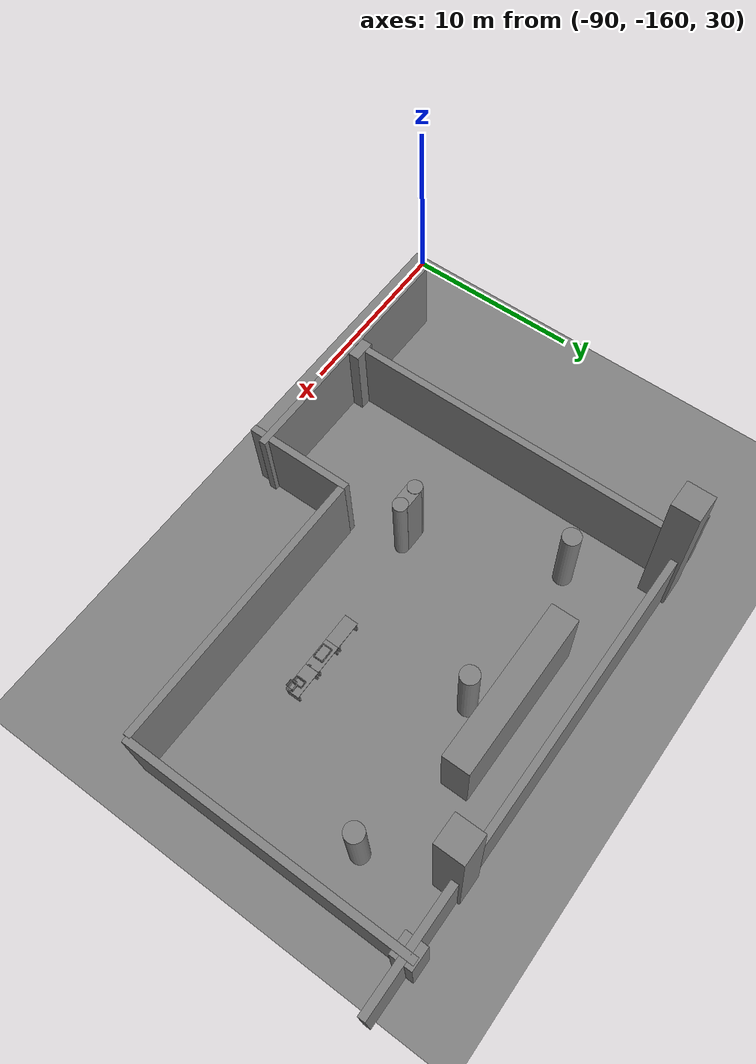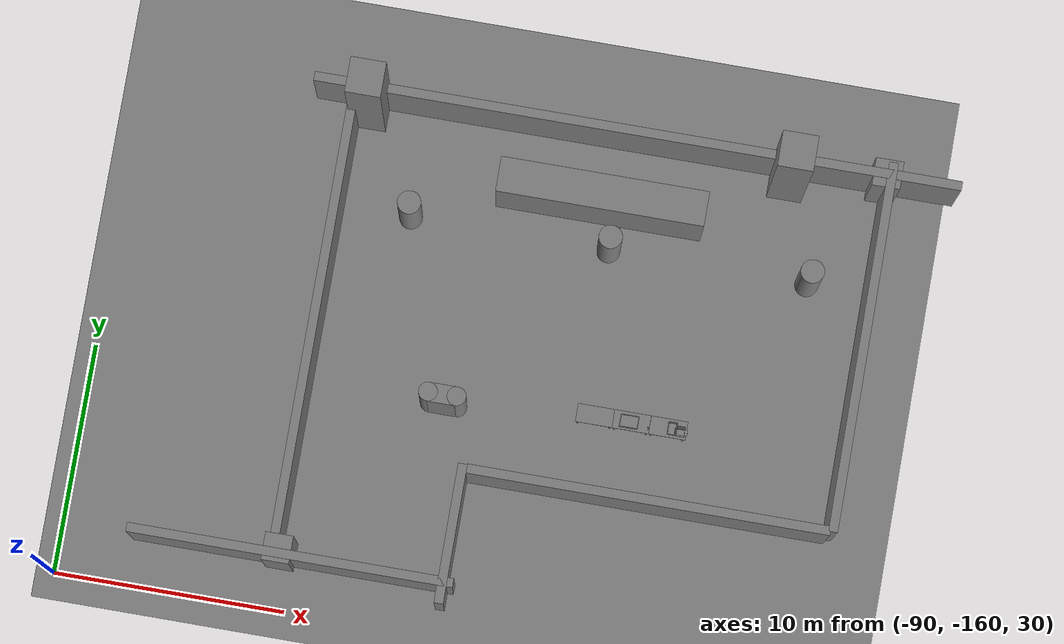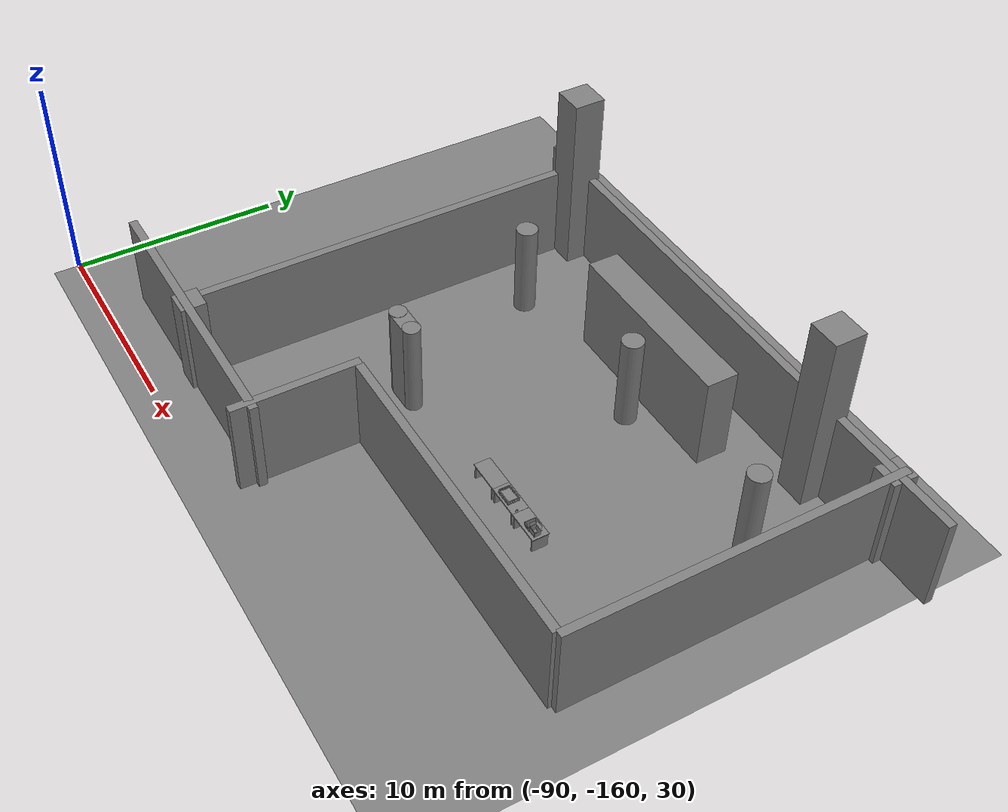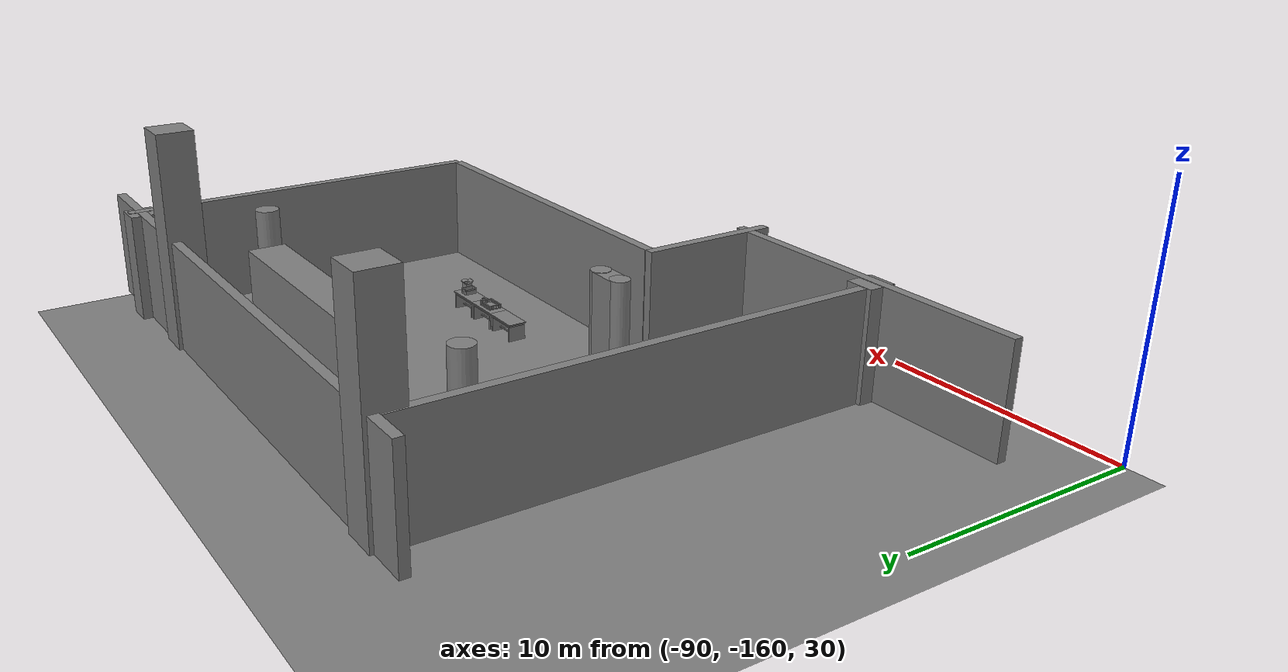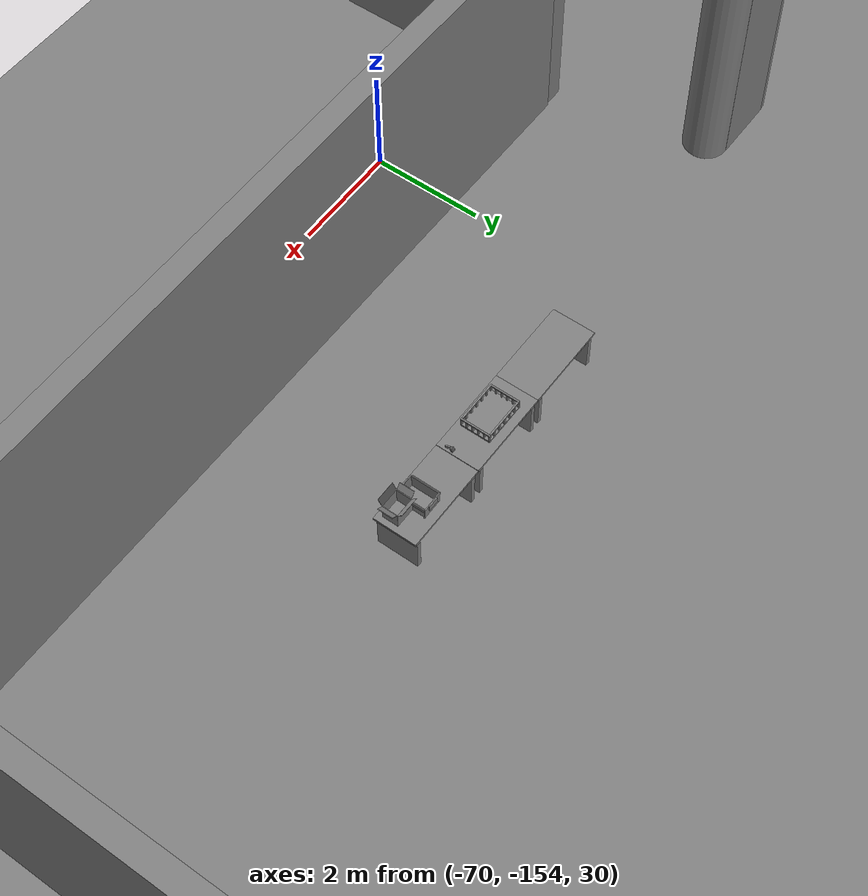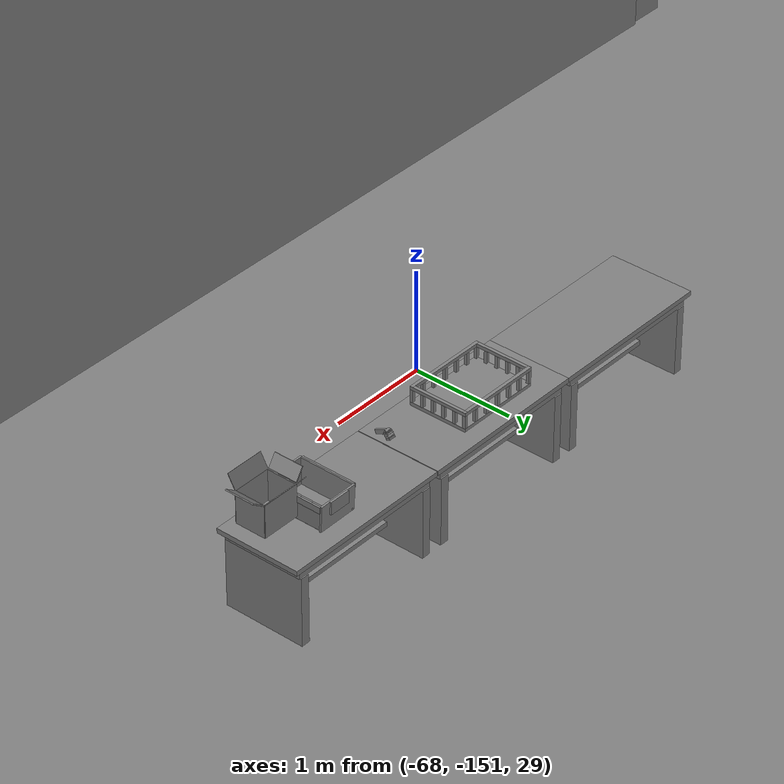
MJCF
<mujoco>
    <option gravity="0.000000000 0.000000000 -9.810000420" timestep="0.0049999999" integrator="implicitfast" density="1.225" viscosity="1.8000001e-05" noslip_iterations="10" iterations="100" sdf_iterations="50">
        <flag multiccd="disable"/>
    </option>
    <size memory="1000M"/>
    <compiler coordinate="local"/>
    <worldbody>
        <light cutoff="30" pos="0 1 1" dir="0 -1 -2"/>
        <light cutoff="30" pos="0 -1 1" dir="0 1 -2"/>
        <body pos="-64.866622925 -149.383972168 30.183746338" euler="89.999992371 89.999946594 0.000000000" name="openloong_gripper_2f85_fix_base_usda_bluebox_01">
            <geom contype="1" conaffinity="1" density="1000" type="box" material="" rgba="0.500000000 0.500000000 0.500000000 1.000000000" solimp="0.899999976 0.949999988 0.001000000" friction="1.000000000 0.005000000 0.000100000" solref="0.020000000 1.000000000" margin="0" condim="3" group="0" pos="0.276596069 0.187225342 0.000061035" quat="0.707107008 0.000077501 0.707106471 0.000077456" size="0.100000001 0.057999998 0.010000000" name="openloong_gripper_2f85_fix_base_usda_geom_D759A73F_80D4_49A0_8FD6_A700831CEACE"/>
            <geom contype="1" conaffinity="1" density="1000" type="box" material="" rgba="0.500000000 0.500000000 0.500000000 1.000000000" solimp="0.899999976 0.949999988 0.001000000" friction="1.000000000 0.005000000 0.000100000" solref="0.020000000 1.000000000" margin="0" condim="3" group="0" pos="0.000000000 0.002883911 0.000000000" quat="1.000000000 0.000000000 0.000000000 0.000000000" size="0.254000008 0.003000000 0.172000006" name="openloong_gripper_2f85_fix_base_usda_geom_54A447F6_ACCC_4E5B_9684_BBADC6A045C3"/>
            <geom contype="1" conaffinity="1" density="1000" type="box" material="" rgba="0.500000000 0.500000000 0.500000000 1.000000000" solimp="0.899999976 0.949999988 0.001000000" friction="1.000000000 0.005000000 0.000100000" solref="0.020000000 1.000000000" margin="0" condim="3" group="0" pos="0.000015259 0.124874115 0.173477173" quat="0.999796450 0.020176515 -0.000000015 0.000000030" size="0.259999990 0.119999997 0.007000000" name="openloong_gripper_2f85_fix_base_usda_geom_09D53EEF_4884_4AA8_A8C0_DDBEDA563CCE"/>
            <geom contype="1" conaffinity="1" density="1000" type="box" material="" rgba="0.500000000 0.500000000 0.500000000 1.000000000" solimp="0.899999976 0.949999988 0.001000000" friction="1.000000000 0.005000000 0.000100000" solref="0.020000000 1.000000000" margin="0" condim="3" group="0" pos="0.000015259 0.124874115 -0.173477173" quat="0.999796450 -0.020176545 -0.000000015 0.000000000" size="0.259999990 0.119999997 0.007000000" name="openloong_gripper_2f85_fix_base_usda_geom_3DBC8762_F548_440A_ADCC_0BAF0650B313"/>
            <geom contype="1" conaffinity="1" density="1000" type="box" material="" rgba="0.500000000 0.500000000 0.500000000 1.000000000" solimp="0.899999976 0.949999988 0.001000000" friction="1.000000000 0.005000000 0.000100000" solref="0.020000000 1.000000000" margin="0" condim="3" group="0" pos="0.000015259 0.214012146 0.188980103" quat="0.999913096 0.013176724 0.000000015 0.000000000" size="0.259999990 0.029999999 0.012500000" name="openloong_gripper_2f85_fix_base_usda_geom_55D5A219_B3B0_4DEE_8045_F41EE3550802"/>
            <geom contype="1" conaffinity="1" density="1000" type="box" material="" rgba="0.500000000 0.500000000 0.500000000 1.000000000" solimp="0.899999976 0.949999988 0.001000000" friction="1.000000000 0.005000000 0.000100000" solref="0.020000000 1.000000000" margin="0" condim="3" group="0" pos="-0.258346558 0.125289917 0.001876831" quat="0.702796996 -0.020792052 0.710783184 0.020769238" size="0.189999998 0.119999997 0.009000000" name="openloong_gripper_2f85_fix_base_usda_geom_2773FEFD_2ED2_4593_BBF0_8649B2C14047"/>
            <geom contype="1" conaffinity="1" density="1000" type="box" material="" rgba="0.500000000 0.500000000 0.500000000 1.000000000" solimp="0.899999976 0.949999988 0.001000000" friction="1.000000000 0.005000000 0.000100000" solref="0.020000000 1.000000000" margin="0" condim="3" group="0" pos="0.000015259 0.214012146 -0.188980103" quat="0.999913096 -0.013176769 0.000000030 0.000000015" size="0.259999990 0.029999999 0.012500000" name="openloong_gripper_2f85_fix_base_usda_geom_9F741026_1108_4C6D_AC3B_A8538A9EE5FC"/>
            <geom contype="1" conaffinity="1" density="1000" type="box" material="" rgba="0.500000000 0.500000000 0.500000000 1.000000000" solimp="0.899999976 0.949999988 0.001000000" friction="1.000000000 0.005000000 0.000100000" solref="0.020000000 1.000000000" margin="0" condim="3" group="0" pos="-0.276596069 0.187225342 0.000061035" quat="0.707106650 0.000077441 0.707106709 0.000077456" size="0.100000001 0.057999998 0.010000000" name="openloong_gripper_2f85_fix_base_usda_geom_5CD92947_1243_4F1F_A14B_3EF5679480DF"/>
            <geom contype="1" conaffinity="1" density="1000" type="box" material="" rgba="0.500000000 0.500000000 0.500000000 1.000000000" solimp="0.899999976 0.949999988 0.001000000" friction="1.000000000 0.005000000 0.000100000" solref="0.020000000 1.000000000" margin="0" condim="3" group="0" pos="0.258346558 0.125289917 0.001876831" quat="0.702851534 0.018856451 0.710823834 -0.019329429" size="0.189999998 0.119999997 0.009000000" name="openloong_gripper_2f85_fix_base_usda_geom_54F96D78_4813_4FA8_B094_66CE2C0A6A09"/>
            <freejoint name="openloong_gripper_2f85_fix_base_usda_bluebox_01_joint"/>
            <site size="0.005000000 0.005000000 0.005000000" rgba="0.500000000 0.500000000 0.500000000 1.000000000" pos="0.000000000 0.000000000 0.000000000" quat="0.999961913 0.008726534 0.000000000 0.000000000" group="0" type="sphere" name="openloong_gripper_2f85_fix_base_usda_bluebox_01site"/>
        </body>
        <body pos="-64.496299744 -149.491867065 30.235729218" euler="0.000000000 0.000000000 89.999946594" name="openloong_gripper_2f85_fix_base_usda_cardboardbox_01">
            <geom contype="1" conaffinity="1" density="1000" type="box" material="" rgba="0.500000000 0.500000000 0.500000000 1.000000000" solimp="0.899999976 0.949999988 0.001000000" friction="1.000000000 0.005000000 0.000100000" solref="0.020000000 1.000000000" margin="0" condim="3" group="0" pos="-0.003166199 -0.004086494 0.005052090" quat="1.000000000 0.000000000 0.000000000 0.000000000" size="0.142499998 0.177500010 0.005000000" name="openloong_gripper_2f85_fix_base_usda_geom_48A2A187_C794_4B2E_9BDF_2DEF5E8F7428"/>
            <geom contype="1" conaffinity="1" density="1000" type="box" material="" rgba="0.500000000 0.500000000 0.500000000 1.000000000" solimp="0.899999976 0.949999988 0.001000000" friction="1.000000000 0.005000000 0.000100000" solref="0.020000000 1.000000000" margin="0" condim="3" group="0" pos="-0.003166199 0.170316696 0.150570869" quat="1.000000000 0.000000000 0.000000000 0.000000000" size="0.142499998 0.005000000 0.149999991" name="openloong_gripper_2f85_fix_base_usda_geom_7DC566B0_8018_484F_9B89_7726109C1F66"/>
            <geom contype="1" conaffinity="1" density="1000" type="box" material="" rgba="0.500000000 0.500000000 0.500000000 1.000000000" solimp="0.899999976 0.949999988 0.001000000" friction="1.000000000 0.005000000 0.000100000" solref="0.020000000 1.000000000" margin="0" condim="3" group="0" pos="-0.147399902 -0.005307198 0.150570869" quat="1.000000000 0.000000000 0.000000000 0.000000000" size="0.005000000 0.177500010 0.149999991" name="openloong_gripper_2f85_fix_base_usda_geom_3B37DC74_64D7_43C6_9623_6CF3597A4BBB"/>
            <geom contype="1" conaffinity="1" density="1000" type="box" material="" rgba="0.500000000 0.500000000 0.500000000 1.000000000" solimp="0.899999976 0.949999988 0.001000000" friction="1.000000000 0.005000000 0.000100000" solref="0.020000000 1.000000000" margin="0" condim="3" group="0" pos="0.140275955 -0.005307198 0.150570869" quat="1.000000000 0.000000000 0.000000000 0.000000000" size="0.005000000 0.177500010 0.149999991" name="openloong_gripper_2f85_fix_base_usda_geom_1927A2FA_B519_41DB_82AB_7ADC888F0101"/>
            <geom contype="1" conaffinity="1" density="1000" type="box" material="" rgba="0.500000000 0.500000000 0.500000000 1.000000000" solimp="0.899999976 0.949999988 0.001000000" friction="1.000000000 0.005000000 0.000100000" solref="0.020000000 1.000000000" margin="0" condim="3" group="0" pos="-0.003166199 -0.181550980 0.150570869" quat="1.000000000 0.000000000 0.000000000 0.000000000" size="0.142499998 0.005000000 0.149999991" name="openloong_gripper_2f85_fix_base_usda_geom_790AFEC6_534F_4750_89A5_88490ED6B286"/>
            <freejoint name="openloong_gripper_2f85_fix_base_usda_cardboardbox_01_joint"/>
            <site size="0.005000000 0.005000000 0.005000000" rgba="0.500000000 0.500000000 0.500000000 1.000000000" pos="0.000000000 0.000000000 0.000000000" quat="0.999961913 0.008726535 0.000000000 0.000000000" group="0" type="sphere" name="openloong_gripper_2f85_fix_base_usda_site_1D2F05EB_63BF_4372_9101_1275451538FD"/>
            <body pos="0.139160156 -0.004048347 0.301930904" euler="-179.999954224 49.383502960 179.999954224" name="openloong_gripper_2f85_fix_base_usda_A1_006">
                <geom contype="1" conaffinity="1" density="1000" type="box" material="" rgba="0.500000000 0.500000000 0.500000000 1.000000000" solimp="0.899999976 0.949999988 0.001000000" friction="1.000000000 0.005000000 0.000100000" solref="0.020000000 1.000000000" margin="0" condim="3" group="0" pos="-0.071587563 0.000009537 0.001745224" quat="0.999999881 0.000000000 0.000000000 0.000000000" size="0.071249999 0.179999992 0.002500000" name="openloong_gripper_2f85_fix_base_usda_geom_93EB53B3_9C53_40C0_B7BF_6E34F676FD4D"/>
                <joint armature="0" stiffness="0.07" damping="0.0099999998" axis="0.000000 1.000000 0.000000" type="hinge" name="openloong_gripper_2f85_fix_base_usda_A1_006"/>
            </body>
            <body pos="-0.145902634 -0.004086494 0.301938057" euler="-180.000000000 -60.000011444 -180.000000000" name="openloong_gripper_2f85_fix_base_usda_A2_006">
                <geom contype="1" conaffinity="1" density="1000" type="box" material="" rgba="0.500000000 0.500000000 0.500000000 1.000000000" solimp="0.899999976 0.949999988 0.001000000" friction="1.000000000 0.005000000 0.000100000" solref="0.020000000 1.000000000" margin="0" condim="3" group="0" pos="0.071268082 0.000009537 0.002717972" quat="0.000002921 0.000000000 -0.000000030 0.999999881" size="0.071249999 0.179999992 0.002500000" name="openloong_gripper_2f85_fix_base_usda_geom_4AD59CC3_D4B0_4773_A689_74B8250923D1"/>
                <joint armature="0" stiffness="0.07" damping="0.0099999998" axis="0.000000 1.000000 0.000000" type="hinge" name="openloong_gripper_2f85_fix_base_usda_A2_006"/>
            </body>
            <body pos="-0.003385544 0.175991058 0.301930904" euler="-125.858116150 -0.000004561 0.000002331" name="openloong_gripper_2f85_fix_base_usda_B2_006">
                <geom contype="1" conaffinity="1" density="1000" type="box" material="" rgba="0.500000000 0.500000000 0.500000000 1.000000000" solimp="0.899999976 0.949999988 0.001000000" friction="1.000000000 0.005000000 0.000100000" solref="0.020000000 1.000000000" margin="0" condim="3" group="0" pos="0.000009537 -0.070939064 -0.002470016" quat="0.999614120 0.027776197 -0.000000015 0.000000030" size="0.137500003 0.064999998 0.005000000" name="openloong_gripper_2f85_fix_base_usda_geom_AD29C72B_ED6D_49D5_A937_292ADD181970"/>
                <joint armature="0" stiffness="0.07" damping="0.0099999998" axis="1.000000 0.000000 0.000000" type="hinge" name="openloong_gripper_2f85_fix_base_usda_B2_006"/>
            </body>
            <body pos="-0.003385544 -0.184140205 0.301938057" euler="147.805557251 0.000000000 0.000000000" name="openloong_gripper_2f85_fix_base_usda_B1_006">
                <geom contype="1" conaffinity="1" density="1000" type="box" material="" rgba="0.500000000 0.500000000 0.500000000 1.000000000" solimp="0.899999976 0.949999988 0.001000000" friction="1.000000000 0.005000000 0.000100000" solref="0.020000000 1.000000000" margin="0" condim="3" group="0" pos="-0.000028610 0.070202351 -0.002703667" quat="0.999614179 -0.027776167 0.000000000 0.000000000" size="0.137500003 0.064999998 0.005000000" name="openloong_gripper_2f85_fix_base_usda_geom_0439DA0D_D85B_430A_868C_8633B5A51025"/>
                <joint armature="0" stiffness="0.07" damping="0.0099999998" axis="1.000000 0.000000 0.000000" type="hinge" name="openloong_gripper_2f85_fix_base_usda_B1_006"/>
            </body>
        </body>
        <body pos="-65.882858276 -149.481979370 30.229999542" euler="-64.487716675 0.000000000 0.000000000" name="openloong_gripper_2f85_fix_base_usda_Barcode">
            <geom contype="1" conaffinity="1" density="1000" type="box" material="" rgba="0.500000000 0.500000000 0.500000000 1.000000000" solimp="0.899999976 0.949999988 0.001000000" friction="1.000000000 0.005000000 0.000100000" solref="0.020000000 1.000000000" margin="0" condim="3" group="0" pos="0.000000000 0.013038635 0.001419067" quat="0.000000000 0.000000000 0.000000000 1.000000119" size="0.034000002 0.010000000 0.017999999" name="openloong_gripper_2f85_fix_base_usda_geom_7FFE959A_1677_476F_AF14_23EC0D2C63BE"/>
            <geom contype="1" conaffinity="1" density="1000" type="box" material="" rgba="0.500000000 0.500000000 0.500000000 1.000000000" solimp="0.899999976 0.949999988 0.001000000" friction="1.000000000 0.005000000 0.000100000" solref="0.020000000 1.000000000" margin="0" condim="3" group="0" pos="0.000000000 -0.035301208 -0.007095337" quat="0.000000000 0.000000000 -0.043619365 0.999048233" size="0.028999999 0.010000000 0.020000000" name="openloong_gripper_2f85_fix_base_usda_geom_E78E91B7_C082_47E4_9E22_179C660BEE35"/>
            <geom contype="1" conaffinity="1" density="1000" type="box" material="" rgba="0.500000000 0.500000000 0.500000000 1.000000000" solimp="0.899999976 0.949999988 0.001000000" friction="1.000000000 0.005000000 0.000100000" solref="0.020000000 1.000000000" margin="0" condim="3" group="0" pos="0.000000000 -0.043411255 -0.011749268" quat="0.922262907 0.386563420 0.000000000 0.000000000" size="0.026000001 0.010000000 0.020000000" name="openloong_gripper_2f85_fix_base_usda_geom_D5907834_CA54_41A1_A008_66BE729091C8"/>
            <geom contype="1" conaffinity="1" density="1000" type="box" material="" rgba="0.500000000 0.500000000 0.500000000 1.000000000" solimp="0.899999976 0.949999988 0.001000000" friction="1.000000000 0.005000000 0.000100000" solref="0.020000000 1.000000000" margin="0" condim="3" group="0" pos="0.000000000 -0.016967773 -0.031860352" quat="0.000000000 0.000000000 0.000000000 1.000000119" size="0.008000000 0.010000000 0.013000000" name="openloong_gripper_2f85_fix_base_usda_geom_C2E38AFF_1398_49E8_9E82_4BAA43D8BAA0"/>
            <geom contype="1" conaffinity="1" density="1000" type="box" material="" rgba="0.500000000 0.500000000 0.500000000 1.000000000" solimp="0.899999976 0.949999988 0.001000000" friction="1.000000000 0.005000000 0.000100000" solref="0.020000000 1.000000000" margin="0" condim="3" group="0" pos="0.000000000 -0.001869202 0.000312805" quat="0.953716993 0.300705761 0.000000000 0.000000000" size="0.032000002 0.010000000 0.018999999" name="openloong_gripper_2f85_fix_base_usda_geom_93D90862_5A91_427B_9B19_5F51CF095FB8"/>
            <geom contype="1" conaffinity="1" density="1000" type="box" material="" rgba="0.500000000 0.500000000 0.500000000 1.000000000" solimp="0.899999976 0.949999988 0.001000000" friction="1.000000000 0.005000000 0.000100000" solref="0.020000000 1.000000000" margin="0" condim="3" group="0" pos="0.000000000 -0.019531250 -0.003173828" quat="0.953716993 0.300705761 0.000000000 0.000000000" size="0.030999999 0.010000000 0.020000000" name="openloong_gripper_2f85_fix_base_usda_geom_201A10D0_1243_43CE_9E31_97ABF4EF442D"/>
            <geom contype="1" conaffinity="1" density="1000" type="box" material="" rgba="0.500000000 0.500000000 0.500000000 1.000000000" solimp="0.899999976 0.949999988 0.001000000" friction="1.000000000 0.005000000 0.000100000" solref="0.020000000 1.000000000" margin="0" condim="3" group="0" pos="0.000000000 -0.035301208 -0.007095337" quat="0.953716993 0.300705761 0.000000000 0.000000000" size="0.028999999 0.010000000 0.020000000" name="openloong_gripper_2f85_fix_base_usda_geom_ED400D33_970F_4E30_BFF9_ADB3342B5A15"/>
            <geom contype="1" conaffinity="1" density="1000" type="box" material="" rgba="0.500000000 0.500000000 0.500000000 1.000000000" solimp="0.899999976 0.949999988 0.001000000" friction="1.000000000 0.005000000 0.000100000" solref="0.020000000 1.000000000" margin="0" condim="3" group="0" pos="0.000000000 -0.042617798 -0.071121216" quat="0.000000000 0.000000000 0.000000000 1.000000119" size="0.013000000 0.021000000 0.059999999" name="openloong_gripper_2f85_fix_base_usda_geom_74DA36EB_045B_44DB_99E5_892C9C210B04"/>
            <freejoint name="openloong_gripper_2f85_fix_base_usda_Barcode_joint"/>
            <site size="0.005000000 0.005000000 0.005000000" rgba="0.500000000 0.500000000 0.500000000 1.000000000" pos="0.000000000 0.000000000 0.000000000" quat="1.000000000 0.000000000 0.000000000 0.000000000" group="0" type="sphere" name="openloong_gripper_2f85_fix_base_usda_Barcode_site"/>
        </body>
        <body pos="-66.745018005 -149.392349243 30.184000015" euler="0.000000000 0.000000000 89.999946594" name="[22332537019515]_Basket_01">
            <geom contype="1" conaffinity="1" density="1000" type="box" material="" rgba="0.500000000 0.500000000 0.500000000 1.000000000" solimp="0.899999976 0.949999988 0.001000000" friction="1.000000000 0.005000000 0.000100000" solref="0.020000000 1.000000000" margin="0" condim="3" group="0" pos="-0.052425385 0.389207840 0.089787483" quat="0.707107008 0.000000000 0.000000000 0.707106411" size="0.014249999 0.014249999 0.059999999" name="[22332537019515]_geom_BE11426C_91B4_48EB_920D_944938B9E0AC"/>
            <geom contype="1" conaffinity="1" density="1000" type="box" material="" rgba="0.500000000 0.500000000 0.500000000 1.000000000" solimp="0.899999976 0.949999988 0.001000000" friction="1.000000000 0.005000000 0.000100000" solref="0.020000000 1.000000000" margin="0" condim="3" group="0" pos="0.264015198 -0.133043289 0.089787483" quat="0.707107008 0.000000000 0.000000000 0.707106411" size="0.014249999 0.014249999 0.059999999" name="[22332537019515]_geom_4DF10627_FAE9_42E4_8B0A_67EE6B0DED4E"/>
            <geom contype="1" conaffinity="1" density="1000" type="box" material="" rgba="0.500000000 0.500000000 0.500000000 1.000000000" solimp="0.899999976 0.949999988 0.001000000" friction="1.000000000 0.005000000 0.000100000" solref="0.020000000 1.000000000" margin="0" condim="3" group="0" pos="-0.264015198 -0.265548706 0.089793205" quat="0.707107008 0.000000000 0.000000000 0.707106411" size="0.014249999 0.014249999 0.059999999" name="[22332537019515]_geom_B15397A6_15D8_4A19_8919_A29718E07CB1"/>
            <geom contype="1" conaffinity="1" density="1000" type="box" material="" rgba="0.500000000 0.500000000 0.500000000 1.000000000" solimp="0.899999976 0.949999988 0.001000000" friction="1.000000000 0.005000000 0.000100000" solref="0.020000000 1.000000000" margin="0" condim="3" group="0" pos="-0.160263062 -0.389322281 0.089793205" quat="0.707107008 0.000000000 0.000000000 0.707106411" size="0.014249999 0.014249999 0.059999999" name="[22332537019515]_geom_F04BD7AA_ADBC_4C5B_9EF1_9F6F50089519"/>
            <geom contype="1" conaffinity="1" density="1000" type="box" material="" rgba="0.500000000 0.500000000 0.500000000 1.000000000" solimp="0.899999976 0.949999988 0.001000000" friction="1.000000000 0.005000000 0.000100000" solref="0.020000000 1.000000000" margin="0" condim="3" group="0" pos="0.162265778 -0.389322281 0.089787483" quat="0.707107008 0.000000000 0.000000000 0.707106411" size="0.014249999 0.014249999 0.059999999" name="[22332537019515]_geom_C63B1326_2000_4F97_BBE2_9A3165D1DA93"/>
            <geom contype="1" conaffinity="1" density="1000" type="box" material="" rgba="0.500000000 0.500000000 0.500000000 1.000000000" solimp="0.899999976 0.949999988 0.001000000" friction="1.000000000 0.005000000 0.000100000" solref="0.020000000 1.000000000" margin="0" condim="3" group="0" pos="0.264015198 0.389207840 0.089787483" quat="0.707107008 0.000000000 0.000000000 0.707106411" size="0.014249999 0.014249999 0.059999999" name="[22332537019515]_geom_25D22B4D_5ABF_4D8A_A421_AE5DCF16305D"/>
            <geom contype="1" conaffinity="1" density="1000" type="box" material="" rgba="0.500000000 0.500000000 0.500000000 1.000000000" solimp="0.899999976 0.949999988 0.001000000" friction="1.000000000 0.005000000 0.000100000" solref="0.020000000 1.000000000" margin="0" condim="3" group="0" pos="-0.264015198 -0.133043289 0.089793205" quat="0.707107008 0.000000000 0.000000000 0.707106411" size="0.014249999 0.014249999 0.059999999" name="[22332537019515]_geom_ED589D44_8C37_4E2A_AA79_61571EAA81AA"/>
            <geom contype="1" conaffinity="1" density="1000" type="box" material="" rgba="0.500000000 0.500000000 0.500000000 1.000000000" solimp="0.899999976 0.949999988 0.001000000" friction="1.000000000 0.005000000 0.000100000" solref="0.020000000 1.000000000" margin="0" condim="3" group="0" pos="-0.264026642 0.269256592 0.089793205" quat="0.707107008 0.000000000 0.000000000 0.707106411" size="0.014249999 0.014249999 0.059999999" name="[22332537019515]_geom_636C4C96_AA1D_4358_8F42_C68AB408040C"/>
            <geom contype="1" conaffinity="1" density="1000" type="box" material="" rgba="0.500000000 0.500000000 0.500000000 1.000000000" solimp="0.899999976 0.949999988 0.001000000" friction="1.000000000 0.005000000 0.000100000" solref="0.020000000 1.000000000" margin="0" condim="3" group="0" pos="0.054462433 0.389207840 0.089787483" quat="0.707107008 0.000000000 0.000000000 0.707106411" size="0.014249999 0.014249999 0.059999999" name="[22332537019515]_geom_224AA29C_4BBB_4B6C_B08F_03525ED77C9E"/>
            <geom contype="1" conaffinity="1" density="1000" type="box" material="" rgba="0.500000000 0.500000000 0.500000000 1.000000000" solimp="0.899999976 0.949999988 0.001000000" friction="1.000000000 0.005000000 0.000100000" solref="0.020000000 1.000000000" margin="0" condim="3" group="0" pos="0.054462433 -0.389322281 0.089787483" quat="0.707107008 0.000000000 0.000000000 0.707106411" size="0.014249999 0.014249999 0.059999999" name="[22332537019515]_geom_C2A20563_85D5_4AC5_A6A1_E6835DF48E11"/>
            <geom contype="1" conaffinity="1" density="1000" type="box" material="" rgba="0.500000000 0.500000000 0.500000000 1.000000000" solimp="0.899999976 0.949999988 0.001000000" friction="1.000000000 0.005000000 0.000100000" solref="0.020000000 1.000000000" margin="0" condim="3" group="0" pos="0.264015198 0.269256592 0.089793205" quat="0.707107008 0.000000000 0.000000000 0.707106411" size="0.014249999 0.014249999 0.059999999" name="[22332537019515]_geom_EF2AB966_6C2B_47E6_9A41_CCCB2BD5F47D"/>
            <geom contype="1" conaffinity="1" density="1000" type="box" material="" rgba="0.500000000 0.500000000 0.500000000 1.000000000" solimp="0.899999976 0.949999988 0.001000000" friction="1.000000000 0.005000000 0.000100000" solref="0.020000000 1.000000000" margin="0" condim="3" group="0" pos="0.264015198 -0.389322281 0.089787483" quat="0.707107008 0.000000000 0.000000000 0.707106411" size="0.014249999 0.014249999 0.059999999" name="[22332537019515]_geom_8F8883A5_93A1_4F25_97DA_B4DB5A39FF7C"/>
            <geom contype="1" conaffinity="1" density="1000" type="box" material="" rgba="0.500000000 0.500000000 0.500000000 1.000000000" solimp="0.899999976 0.949999988 0.001000000" friction="1.000000000 0.005000000 0.000100000" solref="0.020000000 1.000000000" margin="0" condim="3" group="0" pos="0.000000000 0.000000000 0.015998840" quat="0.707107008 0.000000000 0.000000000 0.707106411" size="0.403499991 0.279000014 0.015750000" name="[22332537019515]_geom_ECE4C1EC_81DE_475E_BAD8_1E519AEA23BC"/>
            <geom contype="1" conaffinity="1" density="1000" type="box" material="" rgba="0.500000000 0.500000000 0.500000000 1.000000000" solimp="0.899999976 0.949999988 0.001000000" friction="1.000000000 0.005000000 0.000100000" solref="0.020000000 1.000000000" margin="0" condim="3" group="0" pos="0.000000000 -0.389476776 0.163619041" quat="0.707107008 0.000000000 0.000000000 0.707106411" size="0.015000000 0.277500004 0.015750000" name="[22332537019515]_geom_41A08ABD_92B5_43B9_A28D_0B6568BA7D41"/>
            <geom contype="1" conaffinity="1" density="1000" type="box" material="" rgba="0.500000000 0.500000000 0.500000000 1.000000000" solimp="0.899999976 0.949999988 0.001000000" friction="1.000000000 0.005000000 0.000100000" solref="0.020000000 1.000000000" margin="0" condim="3" group="0" pos="0.162265778 0.389207840 0.089787483" quat="0.707107008 0.000000000 0.000000000 0.707106411" size="0.014249999 0.014249999 0.059999999" name="[22332537019515]_geom_8AE18452_AF48_44BF_843C_CFB8496DBCD8"/>
            <geom contype="1" conaffinity="1" density="1000" type="box" material="" rgba="0.500000000 0.500000000 0.500000000 1.000000000" solimp="0.899999976 0.949999988 0.001000000" friction="1.000000000 0.005000000 0.000100000" solref="0.020000000 1.000000000" margin="0" condim="3" group="0" pos="0.000000000 0.389471054 0.163619041" quat="0.707107008 0.000000000 0.000000000 0.707106411" size="0.015000000 0.277500004 0.015750000" name="[22332537019515]_geom_34959439_5D3A_4899_B7F7_7ECBAB49BC56"/>
            <geom contype="1" conaffinity="1" density="1000" type="box" material="" rgba="0.500000000 0.500000000 0.500000000 1.000000000" solimp="0.899999976 0.949999988 0.001000000" friction="1.000000000 0.005000000 0.000100000" solref="0.020000000 1.000000000" margin="0" condim="3" group="0" pos="-0.263511658 0.000000000 0.163619041" quat="0.707107008 0.000000000 0.000000000 0.707106411" size="0.403499991 0.015000000 0.015750000" name="[22332537019515]_geom_2514768F_EAD1_49F1_AB15_EC77C74BCD22"/>
            <geom contype="1" conaffinity="1" density="1000" type="box" material="" rgba="0.500000000 0.500000000 0.500000000 1.000000000" solimp="0.899999976 0.949999988 0.001000000" friction="1.000000000 0.005000000 0.000100000" solref="0.020000000 1.000000000" margin="0" condim="3" group="0" pos="-0.264015198 0.141334534 0.089793205" quat="0.707107008 0.000000000 0.000000000 0.707106411" size="0.014249999 0.014249999 0.059999999" name="[22332537019515]_geom_AD5161B1_D2E0_4FBA_9D7E_087E1C487324"/>
            <geom contype="1" conaffinity="1" density="1000" type="box" material="" rgba="0.500000000 0.500000000 0.500000000 1.000000000" solimp="0.899999976 0.949999988 0.001000000" friction="1.000000000 0.005000000 0.000100000" solref="0.020000000 1.000000000" margin="0" condim="3" group="0" pos="0.264015198 -0.265548706 0.089787483" quat="0.707107008 0.000000000 0.000000000 0.707106411" size="0.014249999 0.014249999 0.059999999" name="[22332537019515]_geom_8254EEB5_EF50_49D5_8E5F_BC0A9335EF86"/>
            <geom contype="1" conaffinity="1" density="1000" type="box" material="" rgba="0.500000000 0.500000000 0.500000000 1.000000000" solimp="0.899999976 0.949999988 0.001000000" friction="1.000000000 0.005000000 0.000100000" solref="0.020000000 1.000000000" margin="0" condim="3" group="0" pos="-0.160263062 0.389207840 0.089787483" quat="0.707107008 0.000000000 0.000000000 0.707106411" size="0.014249999 0.014249999 0.059999999" name="[22332537019515]_geom_94010B2A_2B36_47DB_9A3F_C2CE5A236DE9"/>
            <geom contype="1" conaffinity="1" density="1000" type="box" material="" rgba="0.500000000 0.500000000 0.500000000 1.000000000" solimp="0.899999976 0.949999988 0.001000000" friction="1.000000000 0.005000000 0.000100000" solref="0.020000000 1.000000000" margin="0" condim="3" group="0" pos="-0.052425385 -0.389322281 0.089787483" quat="0.707107008 0.000000000 0.000000000 0.707106411" size="0.014249999 0.014249999 0.059999999" name="[22332537019515]_geom_02A827A0_D0C4_4C1C_9907_BAE5BCFA97F8"/>
            <geom contype="1" conaffinity="1" density="1000" type="box" material="" rgba="0.500000000 0.500000000 0.500000000 1.000000000" solimp="0.899999976 0.949999988 0.001000000" friction="1.000000000 0.005000000 0.000100000" solref="0.020000000 1.000000000" margin="0" condim="3" group="0" pos="-0.264026642 -0.389322281 0.089793205" quat="0.707107008 0.000000000 0.000000000 0.707106411" size="0.014249999 0.014249999 0.059999999" name="[22332537019515]_geom_2695AEC9_638A_49FB_9642_65B8559B515E"/>
            <geom contype="1" conaffinity="1" density="1000" type="box" material="" rgba="0.500000000 0.500000000 0.500000000 1.000000000" solimp="0.899999976 0.949999988 0.001000000" friction="1.000000000 0.005000000 0.000100000" solref="0.020000000 1.000000000" margin="0" condim="3" group="0" pos="0.264015198 0.141334534 0.089787483" quat="0.707107008 0.000000000 0.000000000 0.707106411" size="0.014249999 0.014249999 0.059999999" name="[22332537019515]_geom_BB2B8DA0_7814_44A2_8EB5_6D3F44DBE016"/>
            <geom contype="1" conaffinity="1" density="1000" type="box" material="" rgba="0.500000000 0.500000000 0.500000000 1.000000000" solimp="0.899999976 0.949999988 0.001000000" friction="1.000000000 0.005000000 0.000100000" solref="0.020000000 1.000000000" margin="0" condim="3" group="0" pos="-0.264015198 0.389207840 0.089793205" quat="0.707107008 0.000000000 0.000000000 0.707106411" size="0.014249999 0.014249999 0.059999999" name="[22332537019515]_geom_10851388_70BA_4D62_8220_93BC3841B648"/>
            <geom contype="1" conaffinity="1" density="1000" type="box" material="" rgba="0.500000000 0.500000000 0.500000000 1.000000000" solimp="0.899999976 0.949999988 0.001000000" friction="1.000000000 0.005000000 0.000100000" solref="0.020000000 1.000000000" margin="0" condim="3" group="0" pos="0.264015198 0.004480362 0.089787483" quat="0.707107008 0.000000000 0.000000000 0.707106411" size="0.014249999 0.014249999 0.059999999" name="[22332537019515]_geom_27131C94_987F_405E_ABED_A57FBAA28AB1"/>
            <geom contype="1" conaffinity="1" density="1000" type="box" material="" rgba="0.500000000 0.500000000 0.500000000 1.000000000" solimp="0.899999976 0.949999988 0.001000000" friction="1.000000000 0.005000000 0.000100000" solref="0.020000000 1.000000000" margin="0" condim="3" group="0" pos="0.263694763 -0.000011444 0.163619041" quat="0.707107008 0.000000000 0.000000000 0.707106411" size="0.403499991 0.015000000 0.015750000" name="[22332537019515]_geom_3C99046F_27C3_4B98_AA27_1271DC04143F"/>
            <geom contype="1" conaffinity="1" density="1000" type="box" material="" rgba="0.500000000 0.500000000 0.500000000 1.000000000" solimp="0.899999976 0.949999988 0.001000000" friction="1.000000000 0.005000000 0.000100000" solref="0.020000000 1.000000000" margin="0" condim="3" group="0" pos="-0.264015198 0.004480362 0.089793205" quat="0.707107008 0.000000000 0.000000000 0.707106411" size="0.014249999 0.014249999 0.059999999" name="[22332537019515]_geom_4202FEB9_5BC4_4268_9A55_19E920FFBE09"/>
            <freejoint name="[22332537019515]_joint_D84AD7B7_96D4_4237_BB60_550FB0D90B33"/>
        </body>
        <body pos="0.000000000 0.000000000 0.000000000" euler="0.000000000 0.000000000 0.000000000" name="Static Objects_Static Objects">
            <geom contype="1" conaffinity="1" density="1000" type="box" material="" rgba="0.500000000 0.500000000 0.500000000 1.000000000" solimp="0.899999976 0.949999988 0.001000000" friction="1.000000000 0.005000000 0.000100000" solref="0.020000000 1.000000000" margin="0" condim="3" group="0" pos="-67.544113159 -149.365814209 29.727830887" quat="0.500000417 0.499999970 0.499999553 0.499999970" size="0.381000012 0.319999993 0.041000001" name="Static Objects_geom_AE0CE5EF_282A_477B_A28F_883E6C4EE3FA"/>
            <geom contype="1" conaffinity="1" density="1000" type="box" material="" rgba="0.500000000 0.500000000 0.500000000 1.000000000" solimp="0.899999976 0.949999988 0.001000000" friction="1.000000000 0.005000000 0.000100000" solref="0.020000000 1.000000000" margin="0" condim="3" group="0" pos="-68.239501953 -149.365814209 30.086868286" quat="0.500000417 0.499999970 0.499999553 0.499999970" size="0.370999992 0.039500002 0.745000005" name="Static Objects_geom_11B38FC2_6F9F_4BBD_99FD_18AF53D4009B"/>
            <geom contype="1" conaffinity="1" density="1000" type="box" material="" rgba="0.500000000 0.500000000 0.500000000 1.000000000" solimp="0.899999976 0.949999988 0.001000000" friction="1.000000000 0.005000000 0.000100000" solref="0.020000000 1.000000000" margin="0" condim="3" group="0" pos="-68.239501953 -149.365814209 30.147235870" quat="0.500000417 0.499999970 0.499999553 0.499999970" size="0.400000006 0.022000000 0.800000012" name="Static Objects_geom_0D867335_DF89_4D39_901A_D1072FC2CDF6"/>
            <geom contype="1" conaffinity="1" density="1000" type="box" material="" rgba="0.500000000 0.500000000 0.500000000 1.000000000" solimp="0.899999976 0.949999988 0.001000000" friction="1.000000000 0.005000000 0.000100000" solref="0.020000000 1.000000000" margin="0" condim="3" group="0" pos="-68.934890747 -149.365814209 29.727830887" quat="0.500000417 0.499999970 0.499999553 0.499999970" size="0.381000012 0.319999993 0.041000001" name="Static Objects_geom_165B2146_3CCC_489A_BDA3_981D402C058A"/>
            <geom contype="1" conaffinity="1" density="1000" type="box" material="" rgba="0.500000000 0.500000000 0.500000000 1.000000000" solimp="0.899999976 0.949999988 0.001000000" friction="1.000000000 0.005000000 0.000100000" solref="0.020000000 1.000000000" margin="0" condim="3" group="0" pos="-68.239501953 -149.365814209 29.561563492" quat="0.500000417 0.499999970 0.499999553 0.499999970" size="0.020000000 0.022000000 0.660000026" name="Static Objects_geom_D2804BDC_B599_4BA3_9779_C9327A4D6CD4"/>
            <geom contype="1" conaffinity="1" density="1000" type="box" material="" rgba="0.500000000 0.500000000 0.500000000 1.000000000" solimp="0.899999976 0.949999988 0.001000000" friction="1.000000000 0.005000000 0.000100000" solref="0.020000000 1.000000000" margin="0" condim="3" group="0" pos="-65.945671082 -149.365814209 29.727830887" quat="0.500000417 0.499999970 0.499999553 0.499999970" size="0.381000012 0.319999993 0.041000001" name="Static Objects_geom_C820AC3A_B7E6_47AB_867D_E98248D10C1D"/>
            <geom contype="1" conaffinity="1" density="1000" type="box" material="" rgba="0.500000000 0.500000000 0.500000000 1.000000000" solimp="0.899999976 0.949999988 0.001000000" friction="1.000000000 0.005000000 0.000100000" solref="0.020000000 1.000000000" margin="0" condim="3" group="0" pos="-66.641059875 -149.365814209 30.086868286" quat="0.500000417 0.499999970 0.499999553 0.499999970" size="0.370999992 0.039500002 0.745000005" name="Static Objects_geom_2C7ADF66_0B12_482B_972B_98BC881416F2"/>
            <geom contype="1" conaffinity="1" density="1000" type="box" material="" rgba="0.500000000 0.500000000 0.500000000 1.000000000" solimp="0.899999976 0.949999988 0.001000000" friction="1.000000000 0.005000000 0.000100000" solref="0.020000000 1.000000000" margin="0" condim="3" group="0" pos="-66.641059875 -149.365814209 30.147235870" quat="0.500000417 0.499999970 0.499999553 0.499999970" size="0.400000006 0.022000000 0.800000012" name="Static Objects_geom_84A79A83_B1EF_44E7_A900_5AD53ADFA0ED"/>
            <geom contype="1" conaffinity="1" density="1000" type="box" material="" rgba="0.500000000 0.500000000 0.500000000 1.000000000" solimp="0.899999976 0.949999988 0.001000000" friction="1.000000000 0.005000000 0.000100000" solref="0.020000000 1.000000000" margin="0" condim="3" group="0" pos="-67.336448669 -149.365814209 29.727830887" quat="0.500000417 0.499999970 0.499999553 0.499999970" size="0.381000012 0.319999993 0.041000001" name="Static Objects_geom_F9CBB4AE_6402_4951_8910_FE25F1DE73BD"/>
            <geom contype="1" conaffinity="1" density="1000" type="box" material="" rgba="0.500000000 0.500000000 0.500000000 1.000000000" solimp="0.899999976 0.949999988 0.001000000" friction="1.000000000 0.005000000 0.000100000" solref="0.020000000 1.000000000" margin="0" condim="3" group="0" pos="-66.641059875 -149.365814209 29.561563492" quat="0.500000417 0.499999970 0.499999553 0.499999970" size="0.020000000 0.022000000 0.660000026" name="Static Objects_geom_483418BE_979E_40E8_BDC8_3AB8A2AE51C3"/>
            <geom contype="1" conaffinity="1" density="1000" type="box" material="" rgba="0.500000000 0.500000000 0.500000000 1.000000000" solimp="0.899999976 0.949999988 0.001000000" friction="1.000000000 0.005000000 0.000100000" solref="0.020000000 1.000000000" margin="0" condim="3" group="0" pos="-64.338577271 -149.365814209 29.727830887" quat="0.500000417 0.499999970 0.499999553 0.499999970" size="0.381000012 0.319999993 0.041000001" name="Static Objects_geom_FC3B02AF_7007_4A1E_98EB_04B4310E0B84"/>
            <geom contype="1" conaffinity="1" density="1000" type="box" material="" rgba="0.500000000 0.500000000 0.500000000 1.000000000" solimp="0.899999976 0.949999988 0.001000000" friction="1.000000000 0.005000000 0.000100000" solref="0.020000000 1.000000000" margin="0" condim="3" group="0" pos="-65.033966064 -149.365814209 30.086868286" quat="0.500000417 0.499999970 0.499999553 0.499999970" size="0.370999992 0.039500002 0.745000005" name="Static Objects_geom_DB9669D0_7575_4266_BF2B_142CBC99DB5A"/>
            <geom contype="1" conaffinity="1" density="1000" type="box" material="" rgba="0.500000000 0.500000000 0.500000000 1.000000000" solimp="0.899999976 0.949999988 0.001000000" friction="1.000000000 0.005000000 0.000100000" solref="0.020000000 1.000000000" margin="0" condim="3" group="0" pos="-65.033966064 -149.365814209 30.147235870" quat="0.500000417 0.499999970 0.499999553 0.499999970" size="0.400000006 0.022000000 0.800000012" name="Static Objects_geom_F860E0BB_F4DE_4A12_93DC_2BDD6177C97E"/>
            <geom contype="1" conaffinity="1" density="1000" type="box" material="" rgba="0.500000000 0.500000000 0.500000000 1.000000000" solimp="0.899999976 0.949999988 0.001000000" friction="1.000000000 0.005000000 0.000100000" solref="0.020000000 1.000000000" margin="0" condim="3" group="0" pos="-65.729354858 -149.365814209 29.727830887" quat="0.500000417 0.499999970 0.499999553 0.499999970" size="0.381000012 0.319999993 0.041000001" name="Static Objects_geom_4302C22D_D5DE_4F53_9605_C2ACC306E7D7"/>
            <geom contype="1" conaffinity="1" density="1000" type="box" material="" rgba="0.500000000 0.500000000 0.500000000 1.000000000" solimp="0.899999976 0.949999988 0.001000000" friction="1.000000000 0.005000000 0.000100000" solref="0.020000000 1.000000000" margin="0" condim="3" group="0" pos="-65.033966064 -149.365814209 29.561563492" quat="0.500000417 0.499999970 0.499999553 0.499999970" size="0.020000000 0.022000000 0.660000026" name="Static Objects_geom_24A90EE2_9EB7_430F_A71A_D2855997E7F6"/>
            <geom contype="1" conaffinity="1" density="1000" type="box" material="" rgba="0.500000000 0.500000000 0.500000000 1.000000000" solimp="0.899999976 0.949999988 0.001000000" friction="1.000000000 0.005000000 0.000100000" solref="0.020000000 1.000000000" margin="0" condim="3" group="0" pos="-61.754566193 -137.853729248 33.906845093" quat="0.707107067 0.000000000 0.000000000 0.707106471" size="0.759999990 0.759999990 4.500000000" name="Static Objects_geom_C5A546A4_58F9_445A_86FF_B8FBCD31F2F9"/>
            <geom contype="1" conaffinity="1" density="1000" type="box" material="" rgba="0.500000000 0.500000000 0.500000000 1.000000000" solimp="0.899999976 0.949999988 0.001000000" friction="1.000000000 0.005000000 0.000100000" solref="0.020000000 1.000000000" margin="0" condim="3" group="0" pos="-57.511135101 -144.927108765 31.707921982" quat="1.000000000 0.000000000 0.000000000 0.000000000" size="0.200000003 8.000000000 2.299999952" name="Static Objects_geom_A6278822_4C77_45DC_99BD_66D1BF5EF739"/>
            <geom contype="1" conaffinity="1" density="1000" type="box" material="" rgba="0.500000000 0.500000000 0.500000000 1.000000000" solimp="0.899999976 0.949999988 0.001000000" friction="1.000000000 0.005000000 0.000100000" solref="0.020000000 1.000000000" margin="0" condim="3" group="0" pos="-80.517646790 -157.574050903 31.688196182" quat="0.707107067 0.000000000 0.000000000 0.707106471" size="0.600000024 0.600000024 2.299999952" name="Static Objects_geom_A106CFE5_16EB_45B7_BA82_4EB8F678F1A4"/>
            <geom contype="1" conaffinity="1" density="1000" type="box" material="" rgba="0.500000000 0.500000000 0.500000000 1.000000000" solimp="0.899999976 0.949999988 0.001000000" friction="1.000000000 0.005000000 0.000100000" solref="0.020000000 1.000000000" margin="0" condim="3" group="0" pos="-80.711044312 -147.414932251 31.666158676" quat="1.000000000 0.000000000 0.000000000 0.000000000" size="0.200000003 10.000000000 2.299999952" name="Static Objects_geom_157F6738_C146_47E2_8CF2_1B51D929D39D"/>
            <geom contype="1" conaffinity="1" density="1000" type="box" material="" rgba="0.500000000 0.500000000 0.500000000 1.000000000" solimp="0.899999976 0.949999988 0.001000000" friction="1.000000000 0.005000000 0.000100000" solref="0.020000000 1.000000000" margin="0" condim="3" group="0" pos="-57.687217712 -137.434692383 31.688196182" quat="0.707107067 0.000000000 0.000000000 0.707106471" size="0.600000024 0.600000024 2.299999952" name="Static Objects_geom_A191CDDA_EED2_45F0_A19E_57A4917CBE91"/>
            <geom contype="1" conaffinity="1" density="1000" type="box" material="" rgba="0.500000000 0.500000000 0.500000000 1.000000000" solimp="0.899999976 0.949999988 0.001000000" friction="1.000000000 0.005000000 0.000100000" solref="0.020000000 1.000000000" margin="0" condim="3" group="0" pos="-69.537033081 -140.263229370 31.714921951" quat="0.707107067 0.000000000 0.000000000 0.707106471" size="0.759999990 4.500000000 2.299999952" name="Static Objects_geom_3B588439_8ECF_4A5D_A948_E9E782A63456"/>
            <geom contype="1" conaffinity="1" density="1000" type="box" material="" rgba="0.500000000 0.500000000 0.500000000 1.000000000" solimp="0.899999976 0.949999988 0.001000000" friction="1.000000000 0.005000000 0.000100000" solref="0.020000000 1.000000000" margin="0" condim="3" group="0" pos="-80.073638916 -137.853713989 33.906845093" quat="0.707107067 0.000000000 0.000000000 0.707106471" size="0.759999990 0.759999990 4.500000000" name="Static Objects_geom_04786B16_5F8D_410C_8271_0E84AE3521E6"/>
            <geom contype="1" conaffinity="1" density="1000" type="box" material="" rgba="0.500000000 0.500000000 0.500000000 1.000000000" solimp="0.899999976 0.949999988 0.001000000" friction="1.000000000 0.005000000 0.000100000" solref="0.020000000 1.000000000" margin="0" condim="3" group="0" pos="-73.406707764 -155.734664917 31.707921982" quat="1.000000000 0.000000000 0.000000000 0.000000000" size="0.200000003 3.000000000 2.299999952" name="Static Objects_geom_EE56E53E_DAB9_463C_8458_BA65AADA523D"/>
            <geom contype="1" conaffinity="1" density="1000" type="box" material="" rgba="0.500000000 0.500000000 0.500000000 1.000000000" solimp="0.899999976 0.949999988 0.001000000" friction="1.000000000 0.005000000 0.000100000" solref="0.020000000 1.000000000" margin="0" condim="3" group="0" pos="-68.497543335 -137.448257446 31.707921982" quat="0.707107067 0.000000000 0.000000000 0.707106471" size="0.200000003 14.000000000 2.299999952" name="Static Objects_geom_809A11A4_EE66_4225_ACDF_9DAB76872E85"/>
            <geom contype="1" conaffinity="1" density="1000" type="cylinder" material="" rgba="0.500000000 0.500000000 0.500000000 1.000000000" solimp="0.899999976 0.949999988 0.001000000" friction="1.000000000 0.005000000 0.000100000" solref="0.020000000 1.000000000" margin="0" condim="3" group="0" pos="-68.868522644 -142.134506226 31.711090088" quat="0.707107067 0.000000000 0.000000000 0.707106471" size="0.509999990 2.299999952 1.000000000" name="Static Objects_geom_E4C1A4BE_8093_4651_AD28_2AF4DD6E7629"/>
            <geom contype="1" conaffinity="1" density="1000" type="plane" material="" rgba="0.500000000 0.500000000 0.500000000 1.000000000" solimp="0.899999976 0.949999988 0.001000000" friction="1.000000000 0.005000000 0.000100000" solref="0.020000000 1.000000000" margin="0" condim="3" group="0" pos="-72.873703003 -147.131927490 29.409669876" quat="1.000000000 0.000000000 0.000000000 0.000000000" size="18.000000000 14.000000000 1.000000000" name="Static Objects_geom_791D1387_B45F_4B3F_8FE9_47D1EFCE7E88"/>
            <geom contype="1" conaffinity="1" density="1000" type="box" material="" rgba="0.500000000 0.500000000 0.500000000 1.000000000" solimp="0.899999976 0.949999988 0.001000000" friction="1.000000000 0.005000000 0.000100000" solref="0.020000000 1.000000000" margin="0" condim="3" group="0" pos="-79.943580627 -157.782272339 31.707921982" quat="0.707107067 0.000000000 0.000000000 0.707106471" size="0.200000003 7.000000000 2.299999952" name="Static Objects_geom_31E092F3_E0E9_4354_82B8_DEE8CB784569"/>
            <geom contype="1" conaffinity="1" density="1000" type="box" material="" rgba="0.500000000 0.500000000 0.500000000 1.000000000" solimp="0.899999976 0.949999988 0.001000000" friction="1.000000000 0.005000000 0.000100000" solref="0.020000000 1.000000000" margin="0" condim="3" group="0" pos="-65.421028137 -152.903442383 31.707921982" quat="0.707107067 0.000000000 0.000000000 0.707106471" size="0.200000003 7.800000191 2.299999952" name="Static Objects_geom_7128EFA6_FB52_4F84_B44C_48562D4379B0"/>
            <geom contype="1" conaffinity="1" density="1000" type="box" material="" rgba="0.500000000 0.500000000 0.500000000 1.000000000" solimp="0.899999976 0.949999988 0.001000000" friction="1.000000000 0.005000000 0.000100000" solref="0.020000000 1.000000000" margin="0" condim="3" group="0" pos="-74.776908875 -149.964416504 31.688196182" quat="1.000000000 0.000000000 0.000000000 0.000000000" size="0.600000024 0.409999996 2.299999952" name="Static Objects_geom_6FE5F7D1_28C3_4986_AC66_3757598F489C"/>
            <geom contype="1" conaffinity="1" density="1000" type="cylinder" material="" rgba="0.500000000 0.500000000 0.500000000 1.000000000" solimp="0.899999976 0.949999988 0.001000000" friction="1.000000000 0.005000000 0.000100000" solref="0.020000000 1.000000000" margin="0" condim="3" group="0" pos="-60.161884308 -142.134506226 31.711090088" quat="0.707107067 0.000000000 0.000000000 0.707106471" size="0.509999990 2.299999952 1.000000000" name="Static Objects_geom_1C95DD49_8787_495E_AADC_6D982B08D177"/>
            <geom contype="1" conaffinity="1" density="1000" type="cylinder" material="" rgba="0.500000000 0.500000000 0.500000000 1.000000000" solimp="0.899999976 0.949999988 0.001000000" friction="1.000000000 0.005000000 0.000100000" solref="0.020000000 1.000000000" margin="0" condim="3" group="0" pos="-75.382453918 -149.963455200 31.711090088" quat="0.707107067 0.000000000 0.000000000 0.707106471" size="0.409999996 2.299999952 1.000000000" name="Static Objects_geom_83F775A6_5B97_4B50_ACCC_00E72FA320A5"/>
            <geom contype="1" conaffinity="1" density="1000" type="cylinder" material="" rgba="0.500000000 0.500000000 0.500000000 1.000000000" solimp="0.899999976 0.949999988 0.001000000" friction="1.000000000 0.005000000 0.000100000" solref="0.020000000 1.000000000" margin="0" condim="3" group="0" pos="-74.154960632 -149.963455200 31.711090088" quat="0.707107067 0.000000000 0.000000000 0.707106471" size="0.409999996 2.299999952 1.000000000" name="Static Objects_geom_8937936D_BB74_436D_99AA_4DF54DEED543"/>
            <geom contype="1" conaffinity="1" density="1000" type="cylinder" material="" rgba="0.500000000 0.500000000 0.500000000 1.000000000" solimp="0.899999976 0.949999988 0.001000000" friction="1.000000000 0.005000000 0.000100000" solref="0.020000000 1.000000000" margin="0" condim="3" group="0" pos="-77.566612244 -142.134506226 31.711090088" quat="0.707107067 0.000000000 0.000000000 0.707106471" size="0.509999990 2.299999952 1.000000000" name="Static Objects_geom_87F563AB_BFF0_48C6_81AA_E25B780DA227"/>
        </body>
        <body pos="-66.291030884 -149.869689941 29.018842697" euler="0.000000000 0.000000000 89.999946594" mocap="true" name="openloong_gripper_2f85_fix_base_usda_leftHandMocap"/>
        <body pos="-66.291030884 -149.869689941 29.018842697" euler="0.000000000 0.000000000 89.999946594" mocap="true" name="openloong_gripper_2f85_fix_base_usda_rightHandMocap"/>
        <body pos="-66.291030884 -149.869689941 30.218843460" euler="0.000000000 0.000000000 89.999946594" name="openloong_gripper_2f85_fix_base_usda_base_link">
            <geom contype="1" conaffinity="1" density="1000" type="mesh" material="" rgba="0.783999979 0.783999979 0.783999979 1.000000000" solimp="0.899999976 0.949999988 0.001000000" friction="1.000000000 0.005000000 0.000100000" solref="0.020000000 1.000000000" margin="0" condim="3" group="3" mesh="base_link" pos="0.000000000 0.000000000 0.000000000" quat="1.000000000 0.000000000 0.000000000 0.000000000" size="1.000000000 1.000000000 1.000000000" name="openloong_gripper_2f85_fix_base_usda__geom_7_81C492EE_2623_4404_9384_8A8A9272531B"/>
            <site size="0.005000000 0.005000000 0.005000000" rgba="0.500000000 0.500000000 0.500000000 1.000000000" pos="0.000000000 0.000000000 0.000000000" quat="1.000000000 0.000000000 0.000000000 0.000000000" group="0" type="sphere" name="openloong_gripper_2f85_fix_base_usda_imu"/>
            <inertial mass="22.447001" pos="-0.005664100 -0.001336700 0.238289997" diaginertia="0.374352545 0.277180195 0.220617250" quat="0.999247074 0.035235517 -0.015086859 0.006023135"/>
            <body pos="0.000000000 0.000000000 0.299997330" euler="0.000000000 0.000000000 0.000000000" name="openloong_gripper_2f85_fix_base_usda_dummy_body">
                <geom contype="1" conaffinity="1" density="1000" type="sphere" material="" rgba="0.783999979 0.783999979 0.783999979 1.000000000" solimp="0.899999976 0.949999988 0.001000000" friction="1.000000000 0.005000000 0.000100000" solref="0.020000000 1.000000000" margin="0" condim="3" group="3" pos="0.000000000 0.000000000 0.000000000" quat="1.000000000 0.000000000 0.000000000 0.000000000" size="0.010000000 0.000000000 0.000000000" name="openloong_gripper_2f85_fix_base_usda__geom_8_5C1AC773_A8F7_4709_993B_1FAA45D621BA"/>
                <joint armature="0.0099999998" stiffness="0" damping="0.1" axis="0.000000 0.000000 1.000000" type="hinge" name="openloong_gripper_2f85_fix_base_usda_dummy_joint"/>
                <site size="0.010000000 0.005000000 0.005000000" rgba="0.500000000 0.500000000 0.500000000 1.000000000" pos="0.000000000 0.000000000 0.000000000" quat="1.000000000 0.000000000 0.000000000 0.000000000" group="3" type="sphere" name="openloong_gripper_2f85_fix_base_usda_dummy_site"/>
            </body>
            <body pos="0.009002686 0.000000000 0.406400681" euler="0.000000000 0.000000000 0.000000000" name="openloong_gripper_2f85_fix_base_usda_Link_head_yaw">
                <geom contype="1" conaffinity="1" density="1000" type="mesh" material="" rgba="0.783999979 0.783999979 0.783999979 1.000000000" solimp="0.899999976 0.949999988 0.001000000" friction="1.000000000 0.005000000 0.000100000" solref="0.020000000 1.000000000" margin="0" condim="3" group="3" mesh="Link_head_yaw" pos="0.000000000 0.000000000 0.000000000" quat="1.000000000 0.000000000 0.000000000 0.000000000" size="1.000000000 1.000000000 1.000000000" name="openloong_gripper_2f85_fix_base_usda__geom_10_CA95961D_1E78_420C_815D_EC2E312CE1BA"/>
                <inertial mass="0.84249002" pos="0.000000000 -0.002081400 0.044801001" diaginertia="0.000700588 0.000629000 0.000553812" quat="0.706933022 -0.015675601 0.015677100 0.706933022"/>
                <body pos="0.000000000 -0.034599304 0.048500061" euler="0.000000000 0.000000000 0.000000000" name="openloong_gripper_2f85_fix_base_usda_Link_head_pitch">
                    <geom contype="1" conaffinity="1" density="1000" type="mesh" material="" rgba="0.783999979 0.783999979 0.783999979 1.000000000" solimp="0.899999976 0.949999988 0.001000000" friction="1.000000000 0.005000000 0.000100000" solref="0.020000000 1.000000000" margin="0" condim="3" group="3" mesh="Link_head_pitch" pos="0.000000000 0.000000000 0.000000000" quat="1.000000000 0.000000000 0.000000000 0.000000000" size="1.000000000 1.000000000 1.000000000" name="openloong_gripper_2f85_fix_base_usda__geom_12_F0D78085_FAF0_4329_B9A7_32CEAF6428C3"/>
                    <inertial mass="1.3943" pos="0.020569000 0.033004001 0.125000000" diaginertia="0.006381400 0.006289940 0.004481460" quat="0.973390222 0.008406822 0.228157058 0.019624906"/>
                    <body pos="0.000000000 0.029998779 0.000000000" euler="0.000000000 0.000000000 0.000000000" name="openloong_gripper_2f85_fix_base_usda_neck_center_body">
                        <site size="0.010000000 0.005000000 0.005000000" rgba="0.500000000 0.500000000 0.500000000 1.000000000" pos="0.000000000 0.000000000 0.000000000" quat="1.000000000 0.000000000 0.000000000 0.000000000" group="3" type="sphere" name="openloong_gripper_2f85_fix_base_usda_neck_center_site"/>
                        <body pos="0.020004272 0.000000000 0.149999619" euler="-0.000002229 39.998176575 -90.000205994" name="openloong_gripper_2f85_fix_base_usda_camera_head">
                            <site size="0.010000000 0.005000000 0.005000000" rgba="0.500000000 0.500000000 0.500000000 1.000000000" pos="0.000000000 0.000000000 0.000000000" quat="1.000000000 0.000000000 0.000000000 0.000000000" group="3" type="sphere" name="openloong_gripper_2f85_fix_base_usda_camera_head_site"/>
                        </body>
                    </body>
                </body>
            </body>
            <body pos="0.003997803 -0.161598206 0.392200470" euler="0.000000000 0.000000000 0.000000000" name="openloong_gripper_2f85_fix_base_usda_Link_arm_r_01">
                <geom contype="1" conaffinity="1" density="1000" type="mesh" material="" rgba="0.783999979 0.783999979 0.783999979 1.000000000" solimp="0.899999976 0.949999988 0.001000000" friction="1.000000000 0.005000000 0.000100000" solref="0.020000000 1.000000000" margin="0" condim="3" group="3" mesh="Link_arm_r_01" pos="0.000000000 0.000000000 0.000000000" quat="1.000000000 0.000000000 0.000000000 0.000000000" size="1.000000000 1.000000000 1.000000000" name="openloong_gripper_2f85_fix_base_usda__geom_14_8CD5A9DC_D47E_4441_BF1B_3A6DE587290D"/>
                <joint armature="0.0099999998" stiffness="0" damping="1" axis="0.000000 -1.000000 0.000000" limited="true" range="-170.000015259 170.000015259" type="hinge" name="openloong_gripper_2f85_fix_base_usda_J_arm_r_01"/>
                <inertial mass="0.75641" pos="0.004494600 -0.038293999 -0.000001874" diaginertia="0.000842990 0.000803050 0.000587120" quat="-0.000163502 0.707098067 0.000812463 0.707115054"/>
                <body pos="-0.041992188 -0.041000366 0.000000000" euler="0.000000000 0.000000000 0.000000000" name="openloong_gripper_2f85_fix_base_usda_Link_arm_r_02">
                    <geom contype="1" conaffinity="1" density="1000" type="mesh" material="" rgba="0.783999979 0.783999979 0.783999979 1.000000000" solimp="0.899999976 0.949999988 0.001000000" friction="1.000000000 0.005000000 0.000100000" solref="0.020000000 1.000000000" margin="0" condim="3" group="3" mesh="Link_arm_r_02" pos="0.000000000 0.000000000 0.000000000" quat="1.000000000 0.000000000 0.000000000 0.000000000" size="1.000000000 1.000000000 1.000000000" name="openloong_gripper_2f85_fix_base_usda__geom_16_4DF8A261_C2F1_4C61_9D1C_BC785F68B138"/>
                    <joint armature="0.0099999998" stiffness="0" damping="1" axis="-1.000000 0.000000 0.000000" limited="true" range="-105.000244141 105.000244141" type="hinge" name="openloong_gripper_2f85_fix_base_usda_J_arm_r_02"/>
                    <inertial mass="0.98500001" pos="0.041999999 -0.067430697 0.000000000" diaginertia="0.002262690 0.001730990 0.001154020" quat="0.500000000 0.500000000 -0.500000000 0.500000000"/>
                    <body pos="0.041992188 -0.122596741 0.000000000" euler="0.000000000 0.000000000 0.000000000" name="openloong_gripper_2f85_fix_base_usda_Link_arm_r_03">
                        <geom contype="1" conaffinity="1" density="1000" type="mesh" material="" rgba="0.783999979 0.783999979 0.783999979 1.000000000" solimp="0.899999976 0.949999988 0.001000000" friction="1.000000000 0.005000000 0.000100000" solref="0.020000000 1.000000000" margin="0" condim="3" group="3" mesh="Link_arm_r_03" pos="0.000000000 0.000000000 0.000000000" quat="1.000000000 0.000000000 0.000000000 0.000000000" size="1.000000000 1.000000000 1.000000000" name="openloong_gripper_2f85_fix_base_usda__geom_18_9F8ABB42_34EB_4FCB_AE2C_E63F44A324C3"/>
                        <joint armature="0.0099999998" stiffness="0" damping="1" axis="0.000000 -1.000000 0.000000" limited="true" range="-170.000015259 170.000015259" type="hinge" name="openloong_gripper_2f85_fix_base_usda_J_arm_r_03"/>
                        <inertial mass="0.95899999" pos="-0.001413580 -0.164663002 0.020757901" diaginertia="0.002101340 0.002064590 0.000754802" quat="0.560480952 0.454391927 -0.443732947 0.531497955"/>
                        <body pos="0.035293579 -0.177406311 0.023998260" euler="0.000000000 0.000000000 0.000000000" name="openloong_gripper_2f85_fix_base_usda_Link_arm_r_04">
                            <geom contype="1" conaffinity="1" density="1000" type="mesh" material="" rgba="0.783999979 0.783999979 0.783999979 1.000000000" solimp="0.899999976 0.949999988 0.001000000" friction="1.000000000 0.005000000 0.000100000" solref="0.020000000 1.000000000" margin="0" condim="3" group="3" mesh="Link_arm_r_04" pos="0.000000000 0.000000000 0.000000000" quat="1.000000000 0.000000000 0.000000000 0.000000000" size="1.000000000 1.000000000 1.000000000" name="openloong_gripper_2f85_fix_base_usda__geom_20_5257EB98_05C5_4CE1_8391_6A42D2F9BA5C"/>
                            <joint armature="0.0099999998" stiffness="0" damping="1" axis="-1.000000 0.000000 0.000000" limited="true" range="0.000000000 170.000015259" type="hinge" name="openloong_gripper_2f85_fix_base_usda_J_arm_r_04"/>
                            <inertial mass="0.60000002" pos="-0.038727000 -0.060766999 -0.021003000" diaginertia="0.001092610 0.000712422 0.000645102" quat="0.327701002 0.632602990 -0.467366993 0.523443997"/>
                            <body pos="-0.035293579 -0.103492737 -0.023998260" euler="0.000000000 0.000000000 0.000000000" name="openloong_gripper_2f85_fix_base_usda_Link_arm_r_05">
                                <geom contype="1" conaffinity="1" density="1000" type="mesh" material="" rgba="0.783999979 0.783999979 0.783999979 1.000000000" solimp="0.899999976 0.949999988 0.001000000" friction="1.000000000 0.005000000 0.000100000" solref="0.020000000 1.000000000" margin="0" condim="3" group="3" mesh="Link_arm_r_05" pos="0.000000000 0.000000000 0.000000000" quat="1.000000000 0.000000000 0.000000000 0.000000000" size="1.000000000 1.000000000 1.000000000" name="openloong_gripper_2f85_fix_base_usda__geom_22_CC4DC36C_CAB3_4B01_BC22_FC10CB7E2333"/>
                                <joint armature="0.0099999998" stiffness="0" damping="1" axis="0.000000 -1.000000 0.000000" limited="true" range="-170.000015259 170.000015259" type="hinge" name="openloong_gripper_2f85_fix_base_usda_J_arm_r_05"/>
                                <inertial mass="0.68976003" pos="0.000032712 -0.068658002 -0.000111780" diaginertia="0.002522510 0.002411100 0.000448695" quat="0.707660973 0.706543028 -0.002603360 0.002470550"/>
                                <body pos="-0.026489258 -0.196502686 0.000000000" euler="0.000000000 0.000000000 0.000000000" name="openloong_gripper_2f85_fix_base_usda_Link_arm_r_06">
                                    <geom contype="1" conaffinity="1" density="1000" type="mesh" material="" rgba="0.783999979 0.783999979 0.783999979 1.000000000" solimp="0.899999976 0.949999988 0.001000000" friction="1.000000000 0.005000000 0.000100000" solref="0.020000000 1.000000000" margin="0" condim="3" group="3" mesh="Link_arm_r_06" pos="0.000000000 0.000000000 0.000000000" quat="1.000000000 0.000000000 0.000000000 0.000000000" size="1.000000000 1.000000000 1.000000000" name="openloong_gripper_2f85_fix_base_usda__geom_24_EB1DA9C1_E9C2_46ED_BCFC_DE435D8DCB87"/>
                                    <joint armature="0.0099999998" stiffness="0" damping="1" axis="1.000000 0.000000 0.000000" limited="true" range="-105.000244141 105.000244141" type="hinge" name="openloong_gripper_2f85_fix_base_usda_J_arm_r_06"/>
                                    <inertial mass="0.28" pos="0.026078001 -0.000000896 0.001663700" diaginertia="0.000156930 0.000145601 0.000104979" quat="0.707080841 0.001851080 0.001883810 0.707127810"/>
                                    <body pos="0.026489258 0.000000000 0.031799316" euler="0.000000000 0.000000000 0.000000000" name="openloong_gripper_2f85_fix_base_usda_Link_arm_r_07">
                                        <geom contype="1" conaffinity="1" density="1000" type="mesh" material="" rgba="0.783999979 0.783999979 0.783999979 1.000000000" solimp="0.899999976 0.949999988 0.001000000" friction="1.000000000 0.005000000 0.000100000" solref="0.020000000 1.000000000" margin="0" condim="3" group="3" mesh="Link_arm_r_07" pos="0.000000000 0.000000000 0.000000000" quat="1.000000000 0.000000000 0.000000000 0.000000000" size="1.000000000 1.000000000 1.000000000" name="openloong_gripper_2f85_fix_base_usda__geom_26_2B278741_AB0B_4213_8ADD_AECFAA8D3F24"/>
                                        <joint armature="0.0099999998" stiffness="0" damping="1" axis="0.000000 0.000000 1.000000" limited="true" range="-60.000133514 60.000133514" type="hinge" name="openloong_gripper_2f85_fix_base_usda_J_arm_r_07"/>
                                        <inertial mass="0.61353999" pos="-0.007859000 -0.158170000 -0.027736001" diaginertia="0.003037610 0.002570910 0.000729379" quat="0.427542925 0.443532884 -0.553093910 0.560867906"/>
                                        <body pos="0.000000000 0.286994934 -0.270000458" euler="150.000350952 -0.000001649 -0.000000442" name="openloong_gripper_2f85_fix_base_usda_camera_wrist_r">
                                            <site size="0.010000000 0.005000000 0.005000000" rgba="0.500000000 0.500000000 0.500000000 1.000000000" pos="0.000000000 0.000000000 0.000000000" quat="1.000000000 0.000000000 0.000000000 0.000000000" group="3" type="sphere" name="openloong_gripper_2f85_fix_base_usda_camera_wrist_r_site"/>
                                        </body>
                                        <body pos="0.000000000 -0.220008850 -0.033002853" euler="0.000000000 0.000000000 179.999969482" name="openloong_gripper_2f85_fix_base_usda_ee_center_body_r">
                                            <site size="0.010000000 0.005000000 0.005000000" rgba="0.500000000 0.500000000 0.500000000 1.000000000" pos="0.000000000 0.000000000 0.000000000" quat="1.000000000 0.000000000 0.000000000 0.000000000" group="3" type="sphere" name="openloong_gripper_2f85_fix_base_usda_ee_center_site_r"/>
                                        </body>
                                        <body pos="0.000000000 -0.066001892 -0.031000137" euler="89.999984741 0.000000000 180.000000000" name="openloong_gripper_2f85_fix_base_usda_zbr_base_link">
                                            <geom contype="1" conaffinity="1" density="1000" type="mesh" material="" rgba="0.783999979 0.783999979 0.783999979 1.000000000" solimp="0.899999976 0.949999988 0.001000000" friction="1.000000000 0.005000000 0.000100000" solref="0.020000000 1.000000000" margin="0" condim="3" group="3" mesh="base" pos="0.000000000 0.000003815 -0.000007629" quat="1.000000000 0.000000000 0.000000000 0.000000000" size="1.000000238 1.000000238 1.000000238" name="openloong_gripper_2f85_fix_base_usda__geom_30_E0D48691_7A54_473A_BECF_9BA77EC98DBE"/>
                                            <inertial mass="0.77744102" pos="0.000000000 -0.000027039 0.035467502" diaginertia="0.000260285 0.000225381 0.000152708" quat="0.999998808 -0.001528488 0.000000000 0.000000000"/>
                                            <body pos="-0.030609138 0.004745484 0.065696731" euler="-89.999984741 -0.000000000 0.000000000" name="openloong_gripper_2f85_fix_base_usda_r_left_driver">
                                                <geom contype="1" conaffinity="1" density="1000" type="mesh" material="" rgba="0.783999979 0.783999979 0.783999979 1.000000000" solimp="0.899999976 0.949999988 0.001000000" friction="1.000000000 0.005000000 0.000100000" solref="0.020000000 1.000000000" margin="0" condim="3" group="3" mesh="driver" pos="0.030609138 0.054901138 -0.004699708" quat="0.707106829 0.707106709 0.000000000 -0.000000000" size="1.000000238 1.000000238 1.000000238" name="openloong_gripper_2f85_fix_base_usda__geom_32_43B06738_8599_42DB_8224_2C8F462E3D79"/>
                                                <joint armature="0.0049999999" stiffness="0" damping="0.1" axis="0.000000 0.000000 1.000000" limited="true" range="0.000000000 51.566200256" type="hinge" name="openloong_gripper_2f85_fix_base_usda_r_left_driver_joint"/>
                                                <inertial mass="0.0089956298" pos="0.000000000 0.017754700 0.001073140" diaginertia="0.000001724 0.000001609 0.000000322" quat="0.681301236 0.732003212 0.000000000 0.000000000"/>
                                                <body pos="-0.031402595 0.004524232 -0.010200503" euler="0.000000000 0.000000000 180.000000000" name="openloong_gripper_2f85_fix_base_usda_r_left_coupler">
                                                    <geom contype="1" conaffinity="1" density="1000" type="mesh" material="" rgba="0.783999979 0.783999979 0.783999979 1.000000000" solimp="0.899999976 0.949999988 0.001000000" friction="1.000000000 0.005000000 0.000100000" solref="0.020000000 1.000000000" margin="0" condim="3" group="3" mesh="coupler" pos="-0.062011734 -0.050354015 0.005500795" quat="0.707106829 -0.707106709 0.000000000 -0.000000000" size="1.000000238 1.000000238 1.000000238" name="openloong_gripper_2f85_fix_base_usda__geom_34_78531FCC_E3E1_4449_83BE_5B325E4BFC7B"/>
                                                    <inertial mass="0.0140974" pos="0.000000000 0.003012090 0.023217499" diaginertia="0.000004162 0.000003522 0.000000888" quat="0.705635548 -0.045590367 0.045590367 0.705635548"/>
                                                </body>
                                            </body>
                                            <body pos="-0.012695315 -0.012001040 0.072212234" euler="-89.999984741 -0.000000000 0.000000000" name="openloong_gripper_2f85_fix_base_usda_r_left_spring_link">
                                                <geom contype="1" conaffinity="1" density="1000" type="mesh" material="" rgba="0.783999979 0.783999979 0.783999979 1.000000000" solimp="0.899999976 0.949999988 0.001000000" friction="1.000000000 0.005000000 0.000100000" solref="0.020000000 1.000000000" margin="0" condim="3" group="3" mesh="spring_link" pos="0.012695315 0.061416641 0.012050631" quat="0.707106829 0.707106709 0.000000000 -0.000000000" size="1.000000238 1.000000238 1.000000238" name="openloong_gripper_2f85_fix_base_usda__geom_36_772F95F1_42C4_4CA2_831A_3D0505E11282"/>
                                                <joint armature="0.001" stiffness="0.050000001" damping="0.00125" axis="0.000000 0.000000 1.000000" limited="true" range="-17.000000000 51.566200256" type="hinge" name="openloong_gripper_2f85_fix_base_usda_r_left_spring_link_joint"/>
                                                <inertial mass="0.0221642" pos="-0.000000009 0.018162400 0.021265799" diaginertia="0.000008969 0.000006717 0.000002639" quat="0.663403213 -0.244737089 0.244737089 0.663403213"/>
                                                <body pos="-0.038208015 -0.042503368 0.002950669" euler="180.000000000 0.000000000 -0.002185660" name="openloong_gripper_2f85_fix_base_usda_r_left_follower">
                                                    <geom contype="1" conaffinity="1" density="1000" type="mesh" material="" rgba="0.783999979 0.783999979 0.783999979 1.000000000" solimp="0.899999976 0.949999988 0.001000000" friction="1.000000000 0.005000000 0.000100000" solref="0.020000000 1.000000000" margin="0" condim="3" group="3" mesh="tongue" pos="0.050918590 -0.103920005 -0.009099962" quat="0.707106829 -0.707106709 0.000000030 0.000000030" size="1.000000238 1.000000238 1.000000238" name="openloong_gripper_2f85_fix_base_usda__geom_40_C0707FEA_FD00_4736_851F_D4826C4572F3"/>
                                                    <geom contype="1" conaffinity="1" density="1000" type="mesh" material="" rgba="0.783999979 0.783999979 0.783999979 1.000000000" solimp="0.899999976 0.949999988 0.001000000" friction="1.000000000 0.005000000 0.000100000" solref="0.020000000 1.000000000" margin="0" condim="3" group="3" mesh="follower" pos="0.050918590 -0.103920005 -0.009099962" quat="0.707106829 -0.707106709 0.000000030 0.000000030" size="1.000000238 1.000000238 1.000000238" name="openloong_gripper_2f85_fix_base_usda__geom_39_CB6B997B_684C_47BB_A663_C6F61723171D"/>
                                                    <joint armature="0.001" stiffness="0" damping="0.1" axis="0.000000 0.000000 1.000000" limited="true" range="-49.999961853 51.566200256" type="hinge" name="openloong_gripper_2f85_fix_base_usda_r_left_follower"/>
                                                    <inertial mass="0.0125222" pos="0.000000000 -0.011046000 0.012478600" diaginertia="0.000002674 0.000002456 0.000000602" quat="0.986436546 0.164143041 0.000000000 0.000000000"/>
                                                    <body pos="-0.037765510 -0.103912376 -0.009099962" euler="-89.999984741 0.000000000 0.000004829" name="openloong_gripper_2f85_fix_base_usda_r_left_pad">
                                                        <geom contype="1" conaffinity="1" density="1000" type="box" material="" rgba="0.550000012 0.550000012 0.550000012 1.000000000" solimp="0.949999988 0.990000010 0.001000000" friction="0.699999988 0.005000000 0.000100000" solref="0.020000000 1.000000000" margin="0" condim="3" group="3" mass="1e-06" pos="0.043243419 0.000003815 0.119995147" quat="0.999999881 0.000000000 0.000000000 0.000000000" size="0.002000001 0.011000003 0.009375002" name="openloong_gripper_2f85_fix_base_usda_r_left_pad1_6F18BA38_138A_45A4_B84A_D441C3DE92F6"/>
                                                        <geom contype="1" conaffinity="1" density="1000" type="box" material="" rgba="0.449999988 0.449999988 0.449999988 1.000000000" solimp="0.949999988 0.990000010 0.001000000" friction="0.600000024 0.005000000 0.000100000" solref="0.020000000 1.000000000" margin="0" condim="3" group="3" mass="1e-06" pos="0.043243419 0.000003815 0.138748199" quat="0.999999881 0.000000000 0.000000000 0.000000000" size="0.002000001 0.011000003 0.009375002" name="openloong_gripper_2f85_fix_base_usda_r_left_pad2_444985CF_8A39_4D0A_A0A5_AC368C761C5E"/>
                                                    </body>
                                                </body>
                                            </body>
                                            <body pos="0.030593880 -0.004753114 0.065696731" euler="89.999984741 0.000000000 180.000000000" name="openloong_gripper_2f85_fix_base_usda_r_right_driver">
                                                <geom contype="1" conaffinity="1" density="1000" type="mesh" material="" rgba="0.783999979 0.783999979 0.783999979 1.000000000" solimp="0.899999976 0.949999988 0.001000000" friction="1.000000000 0.005000000 0.000100000" solref="0.020000000 1.000000000" margin="0" condim="3" group="3" mesh="driver" pos="0.030593880 0.054901138 -0.004699708" quat="0.707106829 0.707106709 0.000000000 0.000000000" size="1.000000238 1.000000238 1.000000238" name="openloong_gripper_2f85_fix_base_usda__geom_42_7261E590_72B1_4CB6_86DA_7674AF3135D6"/>
                                                <joint armature="0.0049999999" stiffness="0" damping="0.1" axis="0.000000 0.000000 1.000000" limited="true" range="0.000000000 51.566200256" type="hinge" name="openloong_gripper_2f85_fix_base_usda_r_right_driver_joint"/>
                                                <inertial mass="0.0089956298" pos="0.000000000 0.017754700 0.001073140" diaginertia="0.000001724 0.000001609 0.000000322" quat="0.681301236 0.732003212 0.000000000 0.000000000"/>
                                                <body pos="-0.031417854 0.004531861 -0.010202411" euler="0.000000000 0.000000000 180.000000000" name="openloong_gripper_2f85_fix_base_usda_r_right_coupler">
                                                    <geom contype="1" conaffinity="1" density="1000" type="mesh" material="" rgba="0.783999979 0.783999979 0.783999979 1.000000000" solimp="0.899999976 0.949999988 0.001000000" friction="1.000000000 0.005000000 0.000100000" solref="0.020000000 1.000000000" margin="0" condim="3" group="3" mesh="coupler" pos="-0.062042251 -0.050376903 0.005500795" quat="0.707106829 -0.707106709 0.000000000 0.000000000" size="1.000000238 1.000000238 1.000000238" name="openloong_gripper_2f85_fix_base_usda__geom_44_1E2E07D1_F596_4B7C_9BFA_9CFD858AB57C"/>
                                                    <inertial mass="0.0140974" pos="0.000000000 0.003012090 0.023217499" diaginertia="0.000004162 0.000003522 0.000000888" quat="0.705635548 -0.045590367 0.045590367 0.705635548"/>
                                                </body>
                                            </body>
                                            <body pos="0.012695315 0.011997226 0.072219864" euler="89.999984741 0.000000000 180.000000000" name="openloong_gripper_2f85_fix_base_usda_r_right_spring_link">
                                                <geom contype="1" conaffinity="1" density="1000" type="mesh" material="" rgba="0.783999979 0.783999979 0.783999979 1.000000000" solimp="0.899999976 0.949999988 0.001000000" friction="1.000000000 0.005000000 0.000100000" solref="0.020000000 1.000000000" margin="0" condim="3" group="3" mesh="spring_link" pos="0.012695315 0.061424270 0.012048724" quat="0.707106829 0.707106709 0.000000000 0.000000000" size="1.000000238 1.000000238 1.000000238" name="openloong_gripper_2f85_fix_base_usda__geom_46_06005B74_9034_4B94_952B_61AF7FA43C41"/>
                                                <joint armature="0.001" stiffness="0.050000001" damping="0.00125" axis="0.000000 0.000000 1.000000" limited="true" range="-17.000000000 51.566200256" type="hinge" name="openloong_gripper_2f85_fix_base_usda_r_right_spring_link_joint"/>
                                                <inertial mass="0.0221642" pos="-0.000000009 0.018162400 0.021265799" diaginertia="0.000008969 0.000006717 0.000002639" quat="0.663403213 -0.244737089 0.244737089 0.663403213"/>
                                                <body pos="-0.038208015 -0.042495739 0.002950669" euler="180.000000000 0.000000000 0.000000000" name="openloong_gripper_2f85_fix_base_usda_r_right_follower">
                                                    <geom contype="1" conaffinity="1" density="1000" type="mesh" material="" rgba="0.783999979 0.783999979 0.783999979 1.000000000" solimp="0.899999976 0.949999988 0.001000000" friction="1.000000000 0.005000000 0.000100000" solref="0.020000000 1.000000000" margin="0" condim="3" group="3" mesh="follower" pos="0.050888073 -0.103927635 -0.009099962" quat="0.707106829 -0.707106709 0.000000000 0.000000000" size="1.000000238 1.000000238 1.000000238" name="openloong_gripper_2f85_fix_base_usda__geom_50_99FB0FEA_8731_4AF2_B3F4_9A5B8F8F0233"/>
                                                    <geom contype="1" conaffinity="1" density="1000" type="mesh" material="" rgba="0.783999979 0.783999979 0.783999979 1.000000000" solimp="0.899999976 0.949999988 0.001000000" friction="1.000000000 0.005000000 0.000100000" solref="0.020000000 1.000000000" margin="0" condim="3" group="3" mesh="tongue" pos="0.050888073 -0.103927635 -0.009099962" quat="0.707106829 -0.707106709 0.000000000 0.000000000" size="1.000000238 1.000000238 1.000000238" name="openloong_gripper_2f85_fix_base_usda__geom_49_36693FEB_A528_468E_8E89_833238FF685F"/>
                                                    <joint armature="0.001" stiffness="0" damping="0.1" axis="0.000000 0.000000 1.000000" limited="true" range="-49.999961853 51.566200256" type="hinge" name="openloong_gripper_2f85_fix_base_usda_r_right_follower_joint"/>
                                                    <inertial mass="0.0125222" pos="0.000000000 -0.011046000 0.012478600" diaginertia="0.000002674 0.000002456 0.000000602" quat="0.986436546 0.164143041 0.000000000 0.000000000"/>
                                                    <body pos="-0.037811287 -0.103927635 -0.009099962" euler="-89.999984741 0.000000000 0.000000000" name="openloong_gripper_2f85_fix_base_usda_r_right_pad">
                                                        <geom contype="1" conaffinity="1" density="1000" type="box" material="" rgba="0.449999988 0.449999988 0.449999988 1.000000000" solimp="0.949999988 0.990000010 0.001000000" friction="0.600000024 0.005000000 0.000100000" solref="0.020000000 1.000000000" margin="0" condim="3" group="3" mass="1e-06" pos="0.043258678 0.000000000 0.138748199" quat="1.000000000 0.000000000 0.000000000 0.000000000" size="0.002000001 0.011000003 0.009375002" name="openloong_gripper_2f85_fix_base_usda_r_right_pad2_99FFD928_A5FD_4CFB_A96E_DCD16B1DBAC3"/>
                                                        <geom contype="1" conaffinity="1" density="1000" type="box" material="" rgba="0.550000012 0.550000012 0.550000012 1.000000000" solimp="0.949999988 0.990000010 0.001000000" friction="0.699999988 0.005000000 0.000100000" solref="0.020000000 1.000000000" margin="0" condim="3" group="3" mass="1e-06" pos="0.043258678 0.000003815 0.120002776" quat="1.000000000 0.000000000 0.000000000 0.000000000" size="0.002000001 0.011000003 0.009375002" name="openloong_gripper_2f85_fix_base_usda_r_right_pad1_B5F4B39A_8696_4C1E_B28D_CFBFFAF63C36"/>
                                                    </body>
                                                </body>
                                            </body>
                                        </body>
                                    </body>
                                </body>
                            </body>
                        </body>
                    </body>
                </body>
            </body>
            <body pos="0.003997803 0.161590576 0.392200470" euler="0.000000000 0.000000000 0.000000000" name="openloong_gripper_2f85_fix_base_usda_Link_arm_l_01">
                <geom contype="1" conaffinity="1" density="1000" type="mesh" material="" rgba="0.783999979 0.783999979 0.783999979 1.000000000" solimp="0.899999976 0.949999988 0.001000000" friction="1.000000000 0.005000000 0.000100000" solref="0.020000000 1.000000000" margin="0" condim="3" group="3" mesh="Link_arm_l_01" pos="0.000000000 0.000000000 0.000000000" quat="1.000000000 0.000000000 0.000000000 0.000000000" size="1.000000000 1.000000000 1.000000000" name="openloong_gripper_2f85_fix_base_usda__geom_52_8341F74F_5CA1_46FA_84EA_A8D3B7D376D9"/>
                <joint armature="0.0099999998" stiffness="0" damping="1" axis="0.000000 1.000000 0.000000" limited="true" range="-170.000015259 170.000015259" type="hinge" name="openloong_gripper_2f85_fix_base_usda_J_arm_l_01"/>
                <inertial mass="0.75640601" pos="-0.004494650 0.038294200 -0.000001874" diaginertia="0.000842986 0.000803053 0.000587115" quat="-0.000812496 0.707115054 0.000163424 0.707098067"/>
                <body pos="0.042007446 0.041000366 0.000000000" euler="0.000000000 0.000000000 0.000000000" name="openloong_gripper_2f85_fix_base_usda_Link_arm_l_02">
                    <geom contype="1" conaffinity="1" density="1000" type="mesh" material="" rgba="0.783999979 0.783999979 0.783999979 1.000000000" solimp="0.899999976 0.949999988 0.001000000" friction="1.000000000 0.005000000 0.000100000" solref="0.020000000 1.000000000" margin="0" condim="3" group="3" mesh="Link_arm_l_02" pos="0.000000000 0.000000000 0.000000000" quat="1.000000000 0.000000000 0.000000000 0.000000000" size="1.000000000 1.000000000 1.000000000" name="openloong_gripper_2f85_fix_base_usda__geom_54_0F8FBA28_5691_4184_8986_C13CBC86F154"/>
                    <joint armature="0.0099999998" stiffness="0" damping="1" axis="-1.000000 0.000000 0.000000" limited="true" range="-105.000244141 105.000244141" type="hinge" name="openloong_gripper_2f85_fix_base_usda_J_arm_l_02"/>
                    <inertial mass="0.98500001" pos="-0.041999999 0.067430697 0.000000000" diaginertia="0.002262690 0.001730990 0.001154020" quat="0.500000000 0.500000000 -0.500000000 0.500000000"/>
                    <body pos="-0.042007446 0.122596741 0.000000000" euler="0.000000000 0.000000000 0.000000000" name="openloong_gripper_2f85_fix_base_usda_Link_arm_l_03">
                        <geom contype="1" conaffinity="1" density="1000" type="mesh" material="" rgba="0.783999979 0.783999979 0.783999979 1.000000000" solimp="0.899999976 0.949999988 0.001000000" friction="1.000000000 0.005000000 0.000100000" solref="0.020000000 1.000000000" margin="0" condim="3" group="3" mesh="Link_arm_l_03" pos="0.000000000 0.000000000 0.000000000" quat="1.000000000 0.000000000 0.000000000 0.000000000" size="1.000000000 1.000000000 1.000000000" name="openloong_gripper_2f85_fix_base_usda__geom_56_C36D81F8_2BF2_4728_9B43_609189D4F911"/>
                        <joint armature="0.0099999998" stiffness="0" damping="1" axis="0.000000 1.000000 0.000000" limited="true" range="-170.000015259 170.000015259" type="hinge" name="openloong_gripper_2f85_fix_base_usda_J_arm_l_03"/>
                        <inertial mass="0.95899999" pos="0.001413580 0.164663002 0.020757901" diaginertia="0.002101340 0.002064590 0.000754802" quat="0.443732947 0.531497955 -0.560480952 0.454391927"/>
                        <body pos="-0.035293579 0.177406311 0.023998260" euler="0.000000000 0.000000000 0.000000000" name="openloong_gripper_2f85_fix_base_usda_Link_arm_l_04">
                            <geom contype="1" conaffinity="1" density="1000" type="mesh" material="" rgba="0.783999979 0.783999979 0.783999979 1.000000000" solimp="0.899999976 0.949999988 0.001000000" friction="1.000000000 0.005000000 0.000100000" solref="0.020000000 1.000000000" margin="0" condim="3" group="3" mesh="Link_arm_l_04" pos="0.000000000 0.000000000 0.000000000" quat="1.000000000 0.000000000 0.000000000 0.000000000" size="1.000000000 1.000000000 1.000000000" name="openloong_gripper_2f85_fix_base_usda__geom_58_54B6E997_FDCE_4F1D_9139_04BED6A05668"/>
                            <joint armature="0.0099999998" stiffness="0" damping="1" axis="1.000000 0.000000 0.000000" limited="true" range="0.000000000 170.000015259" type="hinge" name="openloong_gripper_2f85_fix_base_usda_J_arm_l_04"/>
                            <inertial mass="0.60000002" pos="0.038727000 0.060767200 -0.021003200" diaginertia="0.001092570 0.000712419 0.000645098" quat="0.467370987 0.523440003 -0.327692002 0.632607996"/>
                            <body pos="0.035293579 0.103500366 -0.023998260" euler="0.000000000 0.000000000 0.000000000" name="openloong_gripper_2f85_fix_base_usda_Link_arm_l_05">
                                <geom contype="1" conaffinity="1" density="1000" type="mesh" material="" rgba="0.783999979 0.783999979 0.783999979 1.000000000" solimp="0.899999976 0.949999988 0.001000000" friction="1.000000000 0.005000000 0.000100000" solref="0.020000000 1.000000000" margin="0" condim="3" group="3" mesh="Link_arm_l_05" pos="0.000000000 0.000000000 0.000000000" quat="1.000000000 0.000000000 0.000000000 0.000000000" size="1.000000000 1.000000000 1.000000000" name="openloong_gripper_2f85_fix_base_usda__geom_60_82B3DFCE_9011_41BA_A4D9_4A0330D44EF9"/>
                                <joint armature="0.0099999998" stiffness="0" damping="1" axis="0.000000 1.000000 0.000000" limited="true" range="-170.000015259 170.000015259" type="hinge" name="openloong_gripper_2f85_fix_base_usda_J_arm_l_05"/>
                                <inertial mass="0.68976003" pos="-0.000032712 0.068658002 -0.000111780" diaginertia="0.002522510 0.002411100 0.000448695" quat="0.706543028 0.707660973 0.002470550 -0.002603360"/>
                                <body pos="0.026504517 0.196495056 0.000000000" euler="0.000000000 0.000000000 0.000000000" name="openloong_gripper_2f85_fix_base_usda_Link_arm_l_06">
                                    <geom contype="1" conaffinity="1" density="1000" type="mesh" material="" rgba="0.783999979 0.783999979 0.783999979 1.000000000" solimp="0.899999976 0.949999988 0.001000000" friction="1.000000000 0.005000000 0.000100000" solref="0.020000000 1.000000000" margin="0" condim="3" group="3" mesh="Link_arm_l_06" pos="0.000000000 0.000000000 0.000000000" quat="1.000000000 0.000000000 0.000000000 0.000000000" size="1.000000000 1.000000000 1.000000000" name="openloong_gripper_2f85_fix_base_usda__geom_62_02FB5886_5F5F_4C0B_8F26_2495B3ACE874"/>
                                    <joint armature="0.0099999998" stiffness="0" damping="1" axis="-1.000000 0.000000 0.000000" limited="true" range="-105.000244141 105.000244141" type="hinge" name="openloong_gripper_2f85_fix_base_usda_J_arm_l_06"/>
                                    <inertial mass="0.28" pos="-0.026077701 0.000000896 0.001663730" diaginertia="0.000156927 0.000145598 0.000104981" quat="0.707080841 -0.001851280 -0.001884020 0.707127810"/>
                                    <body pos="-0.026504517 0.000000000 0.031799316" euler="0.000000000 0.000000000 0.000000000" name="openloong_gripper_2f85_fix_base_usda_Link_arm_l_07">
                                        <geom contype="1" conaffinity="1" density="1000" type="mesh" material="" rgba="0.783999979 0.783999979 0.783999979 1.000000000" solimp="0.899999976 0.949999988 0.001000000" friction="1.000000000 0.005000000 0.000100000" solref="0.020000000 1.000000000" margin="0" condim="3" group="3" mesh="Link_arm_l_07" pos="0.000000000 0.000000000 0.000000000" quat="1.000000000 0.000000000 0.000000000 0.000000000" size="1.000000000 1.000000000 1.000000000" name="openloong_gripper_2f85_fix_base_usda__geom_64_1E0E7249_BFA4_4899_B475_70E2E4DBBF92"/>
                                        <joint armature="0.0099999998" stiffness="0" damping="1" axis="0.000000 0.000000 1.000000" limited="true" range="-60.000133514 60.000133514" type="hinge" name="openloong_gripper_2f85_fix_base_usda_J_arm_l_07"/>
                                        <inertial mass="0.61353999" pos="-0.007787200 0.157049999 -0.027733000" diaginertia="0.003037200 0.002570420 0.000729374" quat="0.443562120 0.427539080 -0.560871124 0.553070128"/>
                                        <body pos="0.000000000 -0.286994934 -0.270000458" euler="-150.000350952 0.000001955 179.976669312" name="openloong_gripper_2f85_fix_base_usda_camera_wrist_l">
                                            <site size="0.010000000 0.005000000 0.005000000" rgba="0.500000000 0.500000000 0.500000000 1.000000000" pos="0.000000000 0.000000000 0.000000000" quat="1.000000000 0.000000000 0.000000000 0.000000000" group="3" type="sphere" name="openloong_gripper_2f85_fix_base_usda_camera_wrist_l_site"/>
                                        </body>
                                        <body pos="0.000000000 0.220008850 -0.033002853" euler="0.000000000 0.000000000 0.000000000" name="openloong_gripper_2f85_fix_base_usda_ee_center_body">
                                            <site size="0.010000000 0.005000000 0.005000000" rgba="0.500000000 0.500000000 0.500000000 1.000000000" pos="0.000000000 0.000000000 0.000000000" quat="1.000000000 0.000000000 0.000000000 0.000000000" group="3" type="sphere" name="openloong_gripper_2f85_fix_base_usda_ee_center_site"/>
                                        </body>
                                        <body pos="0.000000000 0.066009521 -0.031000137" euler="-90.000007629 0.000000000 0.000000000" name="openloong_gripper_2f85_fix_base_usda_zbll_base_link">
                                            <geom contype="1" conaffinity="1" density="1000" type="mesh" material="" rgba="0.783999979 0.783999979 0.783999979 1.000000000" solimp="0.899999976 0.949999988 0.001000000" friction="1.000000000 0.005000000 0.000100000" solref="0.020000000 1.000000000" margin="0" condim="3" group="3" mesh="base" pos="0.000000000 0.000000000 0.000000000" quat="1.000000000 0.000000000 0.000000000 0.000000000" size="1.000000000 1.000000000 1.000000000" name="openloong_gripper_2f85_fix_base_usda__geom_68_1397F668_4D24_4A30_9357_AB4B8A4F41E9"/>
                                            <inertial mass="0.77744102" pos="0.000000000 -0.000027039 0.035467502" diaginertia="0.000260285 0.000225381 0.000152708" quat="0.999998808 -0.001528488 0.000000000 0.000000000"/>
                                            <body pos="-0.030578613 0.004755020 0.065696716" euler="-89.999984741 0.000000000 0.000000000" name="openloong_gripper_2f85_fix_base_usda_l_left_driver">
                                                <geom contype="1" conaffinity="1" density="1000" type="mesh" material="" rgba="0.783999979 0.783999979 0.783999979 1.000000000" solimp="0.899999976 0.949999988 0.001000000" friction="1.000000000 0.005000000 0.000100000" solref="0.020000000 1.000000000" margin="0" condim="3" group="3" mesh="driver" pos="0.030609131 0.054901123 -0.004699707" quat="0.707106829 0.707106709 0.000000000 0.000000000" size="1.000000000 1.000000000 1.000000000" name="openloong_gripper_2f85_fix_base_usda__geom_70_A1870443_C898_444F_ADA7_F8EBFB7D8F7C"/>
                                                <joint armature="0.0049999999" stiffness="0" damping="0.1" axis="0.000000 0.000000 1.000000" limited="true" range="0.000000000 51.566200256" type="hinge" name="openloong_gripper_2f85_fix_base_usda_l_left_driver_joint"/>
                                                <inertial mass="0.0089956298" pos="0.000000000 0.017754700 0.001073140" diaginertia="0.000001724 0.000001609 0.000000322" quat="0.681301236 0.732003212 0.000000000 0.000000000"/>
                                                <body pos="-0.031402588 0.004531860 -0.010200500" euler="0.000000000 0.000000000 180.000000000" name="openloong_gripper_2f85_fix_base_usda_l_left_coupler">
                                                    <geom contype="1" conaffinity="1" density="1000" type="mesh" material="" rgba="0.783999979 0.783999979 0.783999979 1.000000000" solimp="0.899999976 0.949999988 0.001000000" friction="1.000000000 0.005000000 0.000100000" solref="0.020000000 1.000000000" margin="0" condim="3" group="3" mesh="coupler" pos="-0.062042236 -0.050369263 0.005500793" quat="0.707106829 -0.707106709 0.000000000 0.000000000" size="1.000000000 1.000000000 1.000000000" name="openloong_gripper_2f85_fix_base_usda__geom_72_7359B234_0FAA_4761_AB5D_D3EC116A17F6"/>
                                                    <inertial mass="0.0140974" pos="0.000000000 0.003012090 0.023217499" diaginertia="0.000004162 0.000003522 0.000000888" quat="0.705635548 -0.045590367 0.045590367 0.705635548"/>
                                                </body>
                                            </body>
                                            <body pos="-0.012680054 -0.011987686 0.072204590" euler="-89.999984741 0.000000000 0.000000000" name="openloong_gripper_2f85_fix_base_usda_l_left_spring_link">
                                                <geom contype="1" conaffinity="1" density="1000" type="mesh" material="" rgba="0.783999979 0.783999979 0.783999979 1.000000000" solimp="0.899999976 0.949999988 0.001000000" friction="1.000000000 0.005000000 0.000100000" solref="0.020000000 1.000000000" margin="0" condim="3" group="3" mesh="spring_link" pos="0.012725830 0.061431885 0.012050629" quat="0.707106829 0.707106709 0.000000000 0.000000000" size="1.000000000 1.000000000 1.000000000" name="openloong_gripper_2f85_fix_base_usda__geom_74_562CD42F_EDBF_43DD_848A_047B7AD3B9F0"/>
                                                <joint armature="0.001" stiffness="0.050000001" damping="0.00125" axis="0.000000 0.000000 1.000000" limited="true" range="-17.000000000 51.566200256" type="hinge" name="openloong_gripper_2f85_fix_base_usda_l_left_spring_link_joint"/>
                                                <inertial mass="0.0221642" pos="-0.000000009 0.018162400 0.021265799" diaginertia="0.000008969 0.000006717 0.000002639" quat="0.663403213 -0.244737089 0.244737089 0.663403213"/>
                                                <body pos="-0.038192749 -0.042495728 0.002950668" euler="180.000000000 0.000000000 -0.002185660" name="openloong_gripper_2f85_fix_base_usda_l_left_follower">
                                                    <geom contype="1" conaffinity="1" density="1000" type="mesh" material="" rgba="0.783999979 0.783999979 0.783999979 1.000000000" solimp="0.899999976 0.949999988 0.001000000" friction="1.000000000 0.005000000 0.000100000" solref="0.020000000 1.000000000" margin="0" condim="3" group="3" mesh="follower" pos="0.050933838 -0.103919983 -0.009098053" quat="0.707106829 -0.707106650 0.000000000 -0.000000030" size="1.000000000 1.000000000 1.000000000" name="openloong_gripper_2f85_fix_base_usda__geom_77_F04F0B71_D4A6_443B_8FF5_B2C5400D22BD"/>
                                                    <geom contype="1" conaffinity="1" density="1000" type="mesh" material="" rgba="0.783999979 0.783999979 0.783999979 1.000000000" solimp="0.899999976 0.949999988 0.001000000" friction="1.000000000 0.005000000 0.000100000" solref="0.020000000 1.000000000" margin="0" condim="3" group="3" mesh="tongue" pos="0.050933838 -0.103919983 -0.009098053" quat="0.707106829 -0.707106650 0.000000000 -0.000000030" size="1.000000000 1.000000000 1.000000000" name="openloong_gripper_2f85_fix_base_usda__geom_78_D1CA708A_8292_4F95_8C6E_880926287135"/>
                                                    <joint armature="0.001" stiffness="0" damping="0.1" axis="0.000000 0.000000 1.000000" limited="true" range="-49.999961853 51.566200256" type="hinge" name="openloong_gripper_2f85_fix_base_usda_l_left_follower"/>
                                                    <inertial mass="0.0125222" pos="0.000000000 -0.011046000 0.012478600" diaginertia="0.000002674 0.000002456 0.000000602" quat="0.986436546 0.164143041 0.000000000 0.000000000"/>
                                                    <body pos="-0.037780762 -0.103919983 -0.009098053" euler="-89.999977112 0.000002415 -0.000002415" name="openloong_gripper_2f85_fix_base_usda_l_left_pad">
                                                        <geom contype="1" conaffinity="1" density="1000" type="box" material="" rgba="0.550000012 0.550000012 0.550000012 1.000000000" solimp="0.949999988 0.990000010 0.001000000" friction="0.699999988 0.005000000 0.000100000" solref="0.020000000 1.000000000" margin="0" condim="3" group="3" mass="1e-06" pos="0.043273926 0.000009537 0.119995117" quat="0.999999881 0.000000000 0.000000000 0.000000000" size="0.002000000 0.011000000 0.009375000" name="openloong_gripper_2f85_fix_base_usda_l_left_pad1_A4FCBE14_3303_4B9E_BD4F_4237E2BD69AA"/>
                                                        <geom contype="1" conaffinity="1" density="1000" type="box" material="" rgba="0.449999988 0.449999988 0.449999988 1.000000000" solimp="0.949999988 0.990000010 0.001000000" friction="0.600000024 0.005000000 0.000100000" solref="0.020000000 1.000000000" margin="0" condim="3" group="3" mass="1e-06" pos="0.043273926 0.000017166 0.138732910" quat="0.999999881 0.000000000 0.000000000 0.000000000" size="0.002000000 0.011000000 0.009375000" name="openloong_gripper_2f85_fix_base_usda_l_left_pad2_67CEACD1_D845_4D60_B43D_1C6E9465E805"/>
                                                    </body>
                                                </body>
                                            </body>
                                            <body pos="0.030609131 -0.004739761 0.065689087" euler="89.999984741 0.000000000 180.000000000" name="openloong_gripper_2f85_fix_base_usda_l_right_driver">
                                                <geom contype="1" conaffinity="1" density="1000" type="mesh" material="" rgba="0.783999979 0.783999979 0.783999979 1.000000000" solimp="0.899999976 0.949999988 0.001000000" friction="1.000000000 0.005000000 0.000100000" solref="0.020000000 1.000000000" margin="0" condim="3" group="3" mesh="driver" pos="0.030593872 0.054901123 -0.004697800" quat="0.707106829 0.707106709 0.000000000 0.000000000" size="1.000000000 1.000000000 1.000000000" name="openloong_gripper_2f85_fix_base_usda__geom_80_0EC4310D_E323_40D7_AC15_AE5AE7F91275"/>
                                                <joint armature="0.0049999999" stiffness="0" damping="0.1" axis="0.000000 0.000000 1.000000" limited="true" range="0.000000000 51.566200256" type="hinge" name="openloong_gripper_2f85_fix_base_usda_l_right_driver_joint"/>
                                                <inertial mass="0.0089956298" pos="0.000000000 0.017754700 0.001073140" diaginertia="0.000001724 0.000001609 0.000000322" quat="0.681301236 0.732003212 0.000000000 0.000000000"/>
                                                <body pos="-0.031433105 0.004531860 -0.010198593" euler="0.000000000 0.000000000 180.000000000" name="openloong_gripper_2f85_fix_base_usda_l_right_coupler">
                                                    <geom contype="1" conaffinity="1" density="1000" type="mesh" material="" rgba="0.783999979 0.783999979 0.783999979 1.000000000" solimp="0.899999976 0.949999988 0.001000000" friction="1.000000000 0.005000000 0.000100000" solref="0.020000000 1.000000000" margin="0" condim="3" group="3" mesh="coupler" pos="-0.062011719 -0.050369263 0.005502701" quat="0.707106829 -0.707106709 0.000000000 0.000000000" size="1.000000000 1.000000000 1.000000000" name="openloong_gripper_2f85_fix_base_usda__geom_82_09FEB09F_F964_40F5_934F_8AB2F2AA343A"/>
                                                    <inertial mass="0.0140974" pos="0.000000000 0.003012090 0.023217499" diaginertia="0.000004162 0.000003522 0.000000888" quat="0.705635548 -0.045590367 0.045590367 0.705635548"/>
                                                </body>
                                            </body>
                                            <body pos="0.012710571 0.012010574 0.072204590" euler="89.999984741 0.000000000 180.000000000" name="openloong_gripper_2f85_fix_base_usda_l_right_spring_link">
                                                <geom contype="1" conaffinity="1" density="1000" type="mesh" material="" rgba="0.783999979 0.783999979 0.783999979 1.000000000" solimp="0.899999976 0.949999988 0.001000000" friction="1.000000000 0.005000000 0.000100000" solref="0.020000000 1.000000000" margin="0" condim="3" group="3" mesh="spring_link" pos="0.012695312 0.061416626 0.012052536" quat="0.707106829 0.707106709 0.000000000 0.000000000" size="1.000000000 1.000000000 1.000000000" name="openloong_gripper_2f85_fix_base_usda__geom_84_BCA3609C_3616_4706_AEE0_D2E19EE7BFF8"/>
                                                <joint armature="0.001" stiffness="0.050000001" damping="0.00125" axis="0.000000 0.000000 1.000000" limited="true" range="-17.000000000 51.566200256" type="hinge" name="openloong_gripper_2f85_fix_base_usda_l_right_spring_link_joint"/>
                                                <inertial mass="0.0221642" pos="-0.000000009 0.018162400 0.021265799" diaginertia="0.000008969 0.000006717 0.000002639" quat="0.663403213 -0.244737089 0.244737089 0.663403213"/>
                                                <body pos="-0.038208008 -0.042503357 0.002952576" euler="180.000000000 0.000000000 0.000000000" name="openloong_gripper_2f85_fix_base_usda_l_right_follower">
                                                    <geom contype="1" conaffinity="1" density="1000" type="mesh" material="" rgba="0.783999979 0.783999979 0.783999979 1.000000000" solimp="0.899999976 0.949999988 0.001000000" friction="1.000000000 0.005000000 0.000100000" solref="0.020000000 1.000000000" margin="0" condim="3" group="3" mesh="tongue" pos="0.050903320 -0.103919983 -0.009099960" quat="0.707106829 -0.707106709 -0.000000030 -0.000000030" size="1.000000000 1.000000000 1.000000000" name="openloong_gripper_2f85_fix_base_usda__geom_87_5E8CBDAA_C019_47C2_B7F4_A420849F8879"/>
                                                    <geom contype="1" conaffinity="1" density="1000" type="mesh" material="" rgba="0.783999979 0.783999979 0.783999979 1.000000000" solimp="0.899999976 0.949999988 0.001000000" friction="1.000000000 0.005000000 0.000100000" solref="0.020000000 1.000000000" margin="0" condim="3" group="3" mesh="follower" pos="0.050903320 -0.103919983 -0.009099960" quat="0.707106829 -0.707106709 -0.000000030 -0.000000030" size="1.000000000 1.000000000 1.000000000" name="openloong_gripper_2f85_fix_base_usda__geom_88_D34DEBC7_E67C_4634_8035_9D71983A4917"/>
                                                    <joint armature="0.001" stiffness="0" damping="0.1" axis="0.000000 0.000000 1.000000" limited="true" range="-49.999961853 51.566200256" type="hinge" name="openloong_gripper_2f85_fix_base_usda_l_right_follower_joint"/>
                                                    <inertial mass="0.0125222" pos="0.000000000 -0.011046000 0.012478600" diaginertia="0.000002674 0.000002456 0.000000602" quat="0.986436546 0.164143041 0.000000000 0.000000000"/>
                                                    <body pos="-0.037796021 -0.103912354 -0.009099960" euler="-89.999984741 -0.000000000 -0.000004830" name="openloong_gripper_2f85_fix_base_usda_l_right_pad">
                                                        <geom contype="1" conaffinity="1" density="1000" type="box" material="" rgba="0.550000012 0.550000012 0.550000012 1.000000000" solimp="0.949999988 0.990000010 0.001000000" friction="0.699999988 0.005000000 0.000100000" solref="0.020000000 1.000000000" margin="0" condim="3" group="3" mass="1e-06" pos="0.043258667 0.000000000 0.119995117" quat="1.000000000 0.000000000 0.000000000 0.000000000" size="0.002000000 0.011000000 0.009375000" name="openloong_gripper_2f85_fix_base_usda_l_right_pad1_18C6F763_6F88_4C4B_8BFB_5A441BC4C311"/>
                                                        <geom contype="1" conaffinity="1" density="1000" type="box" material="" rgba="0.449999988 0.449999988 0.449999988 1.000000000" solimp="0.949999988 0.990000010 0.001000000" friction="0.600000024 0.005000000 0.000100000" solref="0.020000000 1.000000000" margin="0" condim="3" group="3" mass="1e-06" pos="0.043258667 0.000000000 0.138748169" quat="1.000000000 0.000000000 0.000000000 0.000000000" size="0.002000000 0.011000000 0.009375000" name="openloong_gripper_2f85_fix_base_usda_l_right_pad2_B863BFCB_C287_4F11_82C4_C02B968B2EB3"/>
                                                    </body>
                                                </body>
                                            </body>
                                        </body>
                                    </body>
                                </body>
                            </body>
                        </body>
                    </body>
                </body>
            </body>
            <body pos="0.000000000 -0.065246582 0.000000000" euler="0.000000000 0.000000000 0.000000000" name="openloong_gripper_2f85_fix_base_usda_Link_waist_pitch">
                <geom contype="1" conaffinity="1" density="1000" type="mesh" material="" rgba="0.783999979 0.783999979 0.783999979 1.000000000" solimp="0.899999976 0.949999988 0.001000000" friction="1.000000000 0.005000000 0.000100000" solref="0.020000000 1.000000000" margin="0" condim="3" group="3" mesh="Link_waist_pitch" pos="0.000000000 0.000000000 0.000000000" quat="1.000000000 0.000000000 0.000000000 0.000000000" size="1.000000000 1.000000000 1.000000000" name="openloong_gripper_2f85_fix_base_usda__geom_90_65DFDAAB_A2C6_4F52_9AE6_F96D7E5F1DFF"/>
                <inertial mass="2.6963999" pos="-0.000734960 0.049924999 -0.000029695" diaginertia="0.006190620 0.005201250 0.004737120" quat="0.524125040 0.474713057 -0.522095084 0.476820052"/>
                <body pos="-0.063995361 0.065498352 0.000000000" euler="0.000000000 0.000000000 0.000000000" name="openloong_gripper_2f85_fix_base_usda_Link_waist_roll">
                    <geom contype="1" conaffinity="1" density="1000" type="mesh" material="" rgba="0.783999979 0.783999979 0.783999979 1.000000000" solimp="0.899999976 0.949999988 0.001000000" friction="1.000000000 0.005000000 0.000100000" solref="0.020000000 1.000000000" margin="0" condim="3" group="3" mesh="Link_waist_roll" pos="0.000000000 0.000000000 0.000000000" quat="1.000000000 0.000000000 0.000000000 0.000000000" size="1.000000000 1.000000000 1.000000000" name="openloong_gripper_2f85_fix_base_usda__geom_92_ECE64645_5AE5_4CDB_8CBC_AC27C8594325"/>
                    <inertial mass="2.9806001" pos="-0.003742400 -0.001000000 -0.016856000" diaginertia="0.018825000 0.017314700 0.005873970" quat="0.576995134 0.408750087 0.408750087 0.576995134"/>
                    <body pos="0.067520142 0.000000000 -0.097999573" euler="0.000000000 0.000000000 0.000000000" name="openloong_gripper_2f85_fix_base_usda_Link_waist_yaw">
                        <geom contype="1" conaffinity="1" density="1000" type="mesh" material="" rgba="0.783999979 0.783999979 0.783999979 1.000000000" solimp="0.899999976 0.949999988 0.001000000" friction="1.000000000 0.005000000 0.000100000" solref="0.020000000 1.000000000" margin="0" condim="3" group="3" mesh="Link_waist_yaw" pos="0.000000000 0.000000000 0.000000000" quat="1.000000000 0.000000000 0.000000000 0.000000000" size="1.000000000 1.000000000 1.000000000" name="openloong_gripper_2f85_fix_base_usda__geom_94_F9BDE0D9_8493_4C46_B5FE_D9E1BE333B4C"/>
                        <inertial mass="7.3587999" pos="-0.096171997 -0.001000000 -0.057836000" diaginertia="0.109522998 0.089752100 0.032765999" quat="0.571972013 0.571972013 -0.415749997 0.415749997"/>
                        <body pos="-0.087493896 -0.120002747 -0.069000244" euler="0.000000000 0.000000000 0.000000000" name="openloong_gripper_2f85_fix_base_usda_Link_hip_r_roll">
                            <geom contype="1" conaffinity="1" density="1000" type="mesh" material="" rgba="0.783999979 0.783999979 0.783999979 1.000000000" solimp="0.899999976 0.949999988 0.001000000" friction="1.000000000 0.005000000 0.000100000" solref="0.020000000 1.000000000" margin="0" condim="3" group="3" mesh="Link_hip_r_roll" pos="0.000000000 0.000000000 0.000000000" quat="1.000000000 0.000000000 0.000000000 0.000000000" size="1.000000000 1.000000000 1.000000000" name="openloong_gripper_2f85_fix_base_usda__geom_96_87B7E2F2_62DB_4C86_A3AE_007655F0FDF7"/>
                            <inertial mass="2.4333999" pos="0.075724997 -0.001061600 0.016590999" diaginertia="0.004506770 0.003996270 0.003606060" quat="0.357336968 0.610613942 0.606069922 0.363510966"/>
                            <body pos="0.082229614 -0.000999451 -0.009998322" euler="0.000000000 0.000000000 0.000000000" name="openloong_gripper_2f85_fix_base_usda_Link_hip_r_yaw">
                                <geom contype="1" conaffinity="1" density="1000" type="mesh" material="" rgba="0.783999979 0.783999979 0.783999979 1.000000000" solimp="0.899999976 0.949999988 0.001000000" friction="1.000000000 0.005000000 0.000100000" solref="0.020000000 1.000000000" margin="0" condim="3" group="3" mesh="Link_hip_r_yaw" pos="0.000000000 0.000000000 0.000000000" quat="1.000000000 0.000000000 0.000000000 0.000000000" size="1.000000000 1.000000000 1.000000000" name="openloong_gripper_2f85_fix_base_usda__geom_98_3FCEB101_0A8C_4734_9B22_4AAAF58E2D48"/>
                                <inertial mass="3.4303" pos="-0.000000031 -0.007135600 -0.100630000" diaginertia="0.008090100 0.007736500 0.006631600" quat="0.706536055 0.028403703 -0.028403703 0.706536055"/>
                                <body pos="0.000000000 0.036750793 -0.105501175" euler="0.000000000 0.000000000 0.000000000" name="openloong_gripper_2f85_fix_base_usda_Link_hip_r_pitch">
                                    <geom contype="1" conaffinity="1" density="1000" type="mesh" material="" rgba="0.783999979 0.783999979 0.783999979 1.000000000" solimp="0.899999976 0.949999988 0.001000000" friction="1.000000000 0.005000000 0.000100000" solref="0.020000000 1.000000000" margin="0" condim="3" group="3" mesh="Link_hip_r_pitch" pos="0.000000000 0.000000000 0.000000000" quat="1.000000000 0.000000000 0.000000000 0.000000000" size="1.000000000 1.000000000 1.000000000" name="openloong_gripper_2f85_fix_base_usda__geom_100_5B85D6C8_4841_4B11_8142_B0D0F9BB68EB"/>
                                    <inertial mass="5.2378001" pos="0.001085600 -0.054970000 -0.145349994" diaginertia="0.043490201 0.037812300 0.015138500" quat="0.999495864 -0.015916798 0.013696698 0.023812896"/>
                                    <body pos="0.000000000 -0.011253357 -0.400001526" euler="0.000000000 0.000000000 0.000000000" name="openloong_gripper_2f85_fix_base_usda_Link_knee_r_pitch">
                                        <geom contype="1" conaffinity="1" density="1000" type="mesh" material="" rgba="0.783999979 0.783999979 0.783999979 1.000000000" solimp="0.899999976 0.949999988 0.001000000" friction="1.000000000 0.005000000 0.000100000" solref="0.020000000 1.000000000" margin="0" condim="3" group="3" mesh="Link_knee_r_pitch" pos="0.000000000 0.000000000 0.000000000" quat="1.000000000 0.000000000 0.000000000 0.000000000" size="1.000000000 1.000000000 1.000000000" name="openloong_gripper_2f85_fix_base_usda__geom_102_482116C0_6C16_4DC8_9700_77B8685DD38B"/>
                                        <inertial mass="2.9775" pos="-0.009642500 0.000002934 -0.136010006" diaginertia="0.024215899 0.023851801 0.002284610" quat="0.782037616 -0.003061678 0.016178992 0.623013675"/>
                                        <body pos="0.000000000 0.000000000 -0.386999130" euler="0.000000000 0.000000000 0.000000000" name="openloong_gripper_2f85_fix_base_usda_Link_ankle_r_pitch">
                                            <geom contype="1" conaffinity="1" density="1000" type="mesh" material="" rgba="0.783999979 0.783999979 0.783999979 1.000000000" solimp="0.899999976 0.949999988 0.001000000" friction="1.000000000 0.005000000 0.000100000" solref="0.020000000 1.000000000" margin="0" condim="3" group="3" mesh="Link_ankle_r_pitch" pos="0.000000000 0.000000000 0.000000000" quat="1.000000000 0.000000000 0.000000000 0.000000000" size="1.000000000 1.000000000 1.000000000" name="openloong_gripper_2f85_fix_base_usda__geom_104_C8E99DB4_0A2D_4025_8C7A_394600E3BE2E"/>
                                            <inertial mass="0.10145" pos="-0.000000000 -0.000000127 -0.000000025" diaginertia="0.000027175 0.000026565 0.000006112" quat="0.707106829 0.707106829 0.000000000 0.000000000"/>
                                            <body pos="0.000000000 0.000000000 0.000000000" euler="0.000000000 0.000000000 0.000000000" name="openloong_gripper_2f85_fix_base_usda_Link_ankle_r_roll">
                                                <geom contype="1" conaffinity="1" density="1000" type="box" material="" rgba="1.000000000 0.000000000 0.000000000 0.000000000" solimp="0.899999976 0.949999988 0.001000000" friction="1.000000000 0.005000000 0.000100000" solref="0.020000000 1.000000000" margin="0" condim="3" group="3" pos="0.047515869 0.000083923 -0.026544571" quat="1.000000000 0.000000000 0.000000000 0.000000000" size="0.122500002 0.039999999 0.043499999" name="openloong_gripper_2f85_fix_base_usda__geom_106_6D469317_DEA4_4A75_B65D_AB4D52697EA0"/>
                                                <site size="0.123000003 0.041000001 0.044000000" rgba="0.000000000 1.000000000 0.000000000 0.000000000" pos="0.047504615 0.000082667 -0.026545310" quat="1.000000000 0.000000000 0.000000000 0.000000000" group="3" type="box" name="openloong_gripper_2f85_fix_base_usda_rf-tc"/>
                                                <inertial mass="0.75229001" pos="0.041078001 -0.000000089 -0.043908998" diaginertia="0.003659370 0.003646500 0.000416828" quat="0.000000000 0.677034914 0.000000000 0.735950947"/>
                                            </body>
                                        </body>
                                    </body>
                                </body>
                            </body>
                        </body>
                        <body pos="-0.087493896 0.120002747 -0.069000244" euler="0.000000000 0.000000000 0.000000000" name="openloong_gripper_2f85_fix_base_usda_Link_hip_l_roll">
                            <geom contype="1" conaffinity="1" density="1000" type="mesh" material="" rgba="0.783999979 0.783999979 0.783999979 1.000000000" solimp="0.899999976 0.949999988 0.001000000" friction="1.000000000 0.005000000 0.000100000" solref="0.020000000 1.000000000" margin="0" condim="3" group="3" mesh="Link_hip_l_roll" pos="0.000000000 0.000000000 0.000000000" quat="1.000000000 0.000000000 0.000000000 0.000000000" size="1.000000000 1.000000000 1.000000000" name="openloong_gripper_2f85_fix_base_usda__geom_108_B026D5E9_6F9D_4C73_BAFD_149204849233"/>
                            <inertial mass="2.4333999" pos="0.075724997 -0.000938430 0.016590999" diaginertia="0.004257030 0.003974770 0.003377790" quat="0.411751240 0.573205352 0.583885372 0.401216239"/>
                            <body pos="0.082229614 -0.000999451 -0.009998322" euler="0.000000000 0.000000000 0.000000000" name="openloong_gripper_2f85_fix_base_usda_Link_hip_l_yaw">
                                <geom contype="1" conaffinity="1" density="1000" type="mesh" material="" rgba="0.783999979 0.783999979 0.783999979 1.000000000" solimp="0.899999976 0.949999988 0.001000000" friction="1.000000000 0.005000000 0.000100000" solref="0.020000000 1.000000000" margin="0" condim="3" group="3" mesh="Link_hip_l_yaw" pos="0.000000000 0.000000000 0.000000000" quat="1.000000000 0.000000000 0.000000000 0.000000000" size="1.000000000 1.000000000 1.000000000" name="openloong_gripper_2f85_fix_base_usda__geom_110_A675819A_CD1F_48FE_9A35_A51A0C5688FC"/>
                                <inertial mass="3.4303999" pos="-0.000000032 0.007135800 -0.100630000" diaginertia="0.008090100 0.007736500 0.006631500" quat="0.706536174 -0.028401807 0.028401807 0.706536174"/>
                                <body pos="0.000000000 -0.036758423 -0.105501175" euler="0.000000000 0.000000000 0.000000000" name="openloong_gripper_2f85_fix_base_usda_Link_hip_l_pitch">
                                    <geom contype="1" conaffinity="1" density="1000" type="mesh" material="" rgba="0.783999979 0.783999979 0.783999979 1.000000000" solimp="0.899999976 0.949999988 0.001000000" friction="1.000000000 0.005000000 0.000100000" solref="0.020000000 1.000000000" margin="0" condim="3" group="3" mesh="Link_hip_l_pitch" pos="0.000000000 0.000000000 0.000000000" quat="1.000000000 0.000000000 0.000000000 0.000000000" size="1.000000000 1.000000000 1.000000000" name="openloong_gripper_2f85_fix_base_usda__geom_112_BC6DFAB7_3B01_4703_8A55_BA9C4F13E163"/>
                                    <inertial mass="5.2378001" pos="0.001085600 0.054970000 -0.145349994" diaginertia="0.043490201 0.037812300 0.015138500" quat="0.999495745 0.015916597 0.013696796 -0.023821594"/>
                                    <body pos="0.000000000 0.011260986 -0.400001526" euler="0.000000000 0.000000000 0.000000000" name="openloong_gripper_2f85_fix_base_usda_Link_knee_l_pitch">
                                        <geom contype="1" conaffinity="1" density="1000" type="mesh" material="" rgba="0.783999979 0.783999979 0.783999979 1.000000000" solimp="0.899999976 0.949999988 0.001000000" friction="1.000000000 0.005000000 0.000100000" solref="0.020000000 1.000000000" margin="0" condim="3" group="3" mesh="Link_knee_l_pitch" pos="0.000000000 0.000000000 0.000000000" quat="1.000000000 0.000000000 0.000000000 0.000000000" size="1.000000000 1.000000000 1.000000000" name="openloong_gripper_2f85_fix_base_usda__geom_114_394CBC75_EF88_4349_AE34_D21A5F78F57D"/>
                                        <inertial mass="2.9775" pos="-0.009642500 -0.000002868 -0.136010006" diaginertia="0.024214899 0.023850800 0.002284610" quat="0.623014212 0.016178306 -0.003060011 0.782037318"/>
                                        <body pos="0.000000000 0.000000000 -0.386999130" euler="0.000000000 0.000000000 0.000000000" name="openloong_gripper_2f85_fix_base_usda_Link_ankle_l_pitch">
                                            <geom contype="1" conaffinity="1" density="1000" type="mesh" material="" rgba="0.783999979 0.783999979 0.783999979 1.000000000" solimp="0.899999976 0.949999988 0.001000000" friction="1.000000000 0.005000000 0.000100000" solref="0.020000000 1.000000000" margin="0" condim="3" group="3" mesh="Link_ankle_l_pitch" pos="0.000000000 0.000000000 0.000000000" quat="1.000000000 0.000000000 0.000000000 0.000000000" size="1.000000000 1.000000000 1.000000000" name="openloong_gripper_2f85_fix_base_usda__geom_116_C540A47E_C369_4F24_AC51_40CEAC56864D"/>
                                            <inertial mass="0.10145" pos="-0.000000000 0.000000127 0.000000067" diaginertia="0.000027175 0.000026565 0.000006112" quat="0.707106829 0.707106829 0.000000000 0.000000000"/>
                                            <body pos="0.000000000 0.000000000 0.000000000" euler="0.000000000 0.000000000 0.000000000" name="openloong_gripper_2f85_fix_base_usda_Link_ankle_l_roll">
                                                <geom contype="1" conaffinity="1" density="1000" type="box" material="" rgba="1.000000000 0.000000000 0.000000000 0.000000000" solimp="0.899999976 0.949999988 0.001000000" friction="1.000000000 0.005000000 0.000100000" solref="0.020000000 1.000000000" margin="0" condim="3" group="3" pos="0.047515869 0.001220703 -0.027221680" quat="1.000000000 0.000000000 0.000000000 0.000000000" size="0.122500002 0.040199999 0.044199999" name="openloong_gripper_2f85_fix_base_usda__geom_118_26B91243_265E_4362_8BA7_C5379E335B61"/>
                                                <site size="0.123000003 0.041000001 0.045000002" rgba="0.000000000 1.000000000 0.000000000 0.000000000" pos="0.047499999 0.001220864 -0.027223988" quat="1.000000000 0.000000000 0.000000000 0.000000000" group="3" type="box" name="openloong_gripper_2f85_fix_base_usda_lf-tc"/>
                                                <inertial mass="0.75228798" pos="0.041076999 -0.000000029 -0.043908998" diaginertia="0.003659370 0.003646500 0.000416828" quat="0.000000000 0.677034914 0.000000000 0.735950947"/>
                                            </body>
                                        </body>
                                    </body>
                                </body>
                            </body>
                        </body>
                    </body>
                </body>
            </body>
        </body>
    </worldbody>
    <tendon>
        <fixed name="openloong_gripper_2f85_fix_base_usda_l_split">
            <joint joint="openloong_gripper_2f85_fix_base_usda_l_right_driver_joint" coef="0.48500001"/>
            <joint joint="openloong_gripper_2f85_fix_base_usda_l_left_driver_joint" coef="0.48500001"/>
        </fixed>
        <fixed name="openloong_gripper_2f85_fix_base_usda_r_split">
            <joint joint="openloong_gripper_2f85_fix_base_usda_r_right_driver_joint" coef="0.48500001"/>
            <joint joint="openloong_gripper_2f85_fix_base_usda_r_left_driver_joint" coef="0.48500001"/>
        </fixed>
    </tendon>
    <actuator>
        <position ctrllimited="true" ctrlrange="-2.96706 2.96706" forcelimited="true" forcerange="-80 80" joint="openloong_gripper_2f85_fix_base_usda_J_arm_l_01" kp="200" kv="20" name="openloong_gripper_2f85_fix_base_usda_P_arm_l_01"/>
        <position ctrllimited="true" ctrlrange="-1.8326 1.8326" forcelimited="true" forcerange="-80 80" joint="openloong_gripper_2f85_fix_base_usda_J_arm_l_02" kp="200" kv="20" name="openloong_gripper_2f85_fix_base_usda_P_arm_l_02"/>
        <position ctrllimited="true" ctrlrange="-2.96706 2.96706" forcelimited="true" forcerange="-48 48" joint="openloong_gripper_2f85_fix_base_usda_J_arm_l_03" kp="200" kv="20" name="openloong_gripper_2f85_fix_base_usda_P_arm_l_03"/>
        <position ctrllimited="true" ctrlrange="0 2.96706" forcelimited="true" forcerange="-48 48" joint="openloong_gripper_2f85_fix_base_usda_J_arm_l_04" kp="200" kv="20" name="openloong_gripper_2f85_fix_base_usda_P_arm_l_04"/>
        <position ctrllimited="true" ctrlrange="-2.96706 2.96706" forcelimited="true" forcerange="-12.4 12.4" joint="openloong_gripper_2f85_fix_base_usda_J_arm_l_05" kp="200" kv="20" name="openloong_gripper_2f85_fix_base_usda_P_arm_l_05"/>
        <position ctrllimited="true" ctrlrange="-1.8326 1.8326" forcelimited="true" forcerange="-12.4 12.4" joint="openloong_gripper_2f85_fix_base_usda_J_arm_l_06" kp="200" kv="20" name="openloong_gripper_2f85_fix_base_usda_P_arm_l_06"/>
        <position ctrllimited="true" ctrlrange="-1.0472 1.0472" forcelimited="true" forcerange="-12.4 12.4" joint="openloong_gripper_2f85_fix_base_usda_J_arm_l_07" kp="200" kv="20" name="openloong_gripper_2f85_fix_base_usda_P_arm_l_07"/>
        <motor ctrllimited="true" ctrlrange="-80 80" gear="1" joint="openloong_gripper_2f85_fix_base_usda_J_arm_l_01" name="openloong_gripper_2f85_fix_base_usda_M_arm_l_01"/>
        <motor ctrllimited="true" ctrlrange="-80 80" gear="1" joint="openloong_gripper_2f85_fix_base_usda_J_arm_l_02" name="openloong_gripper_2f85_fix_base_usda_M_arm_l_02"/>
        <motor ctrllimited="true" ctrlrange="-48 48" gear="1" joint="openloong_gripper_2f85_fix_base_usda_J_arm_l_03" name="openloong_gripper_2f85_fix_base_usda_M_arm_l_03"/>
        <motor ctrllimited="true" ctrlrange="-48 48" gear="1" joint="openloong_gripper_2f85_fix_base_usda_J_arm_l_04" name="openloong_gripper_2f85_fix_base_usda_M_arm_l_04"/>
        <motor ctrllimited="true" ctrlrange="-12.4 12.4" gear="1" joint="openloong_gripper_2f85_fix_base_usda_J_arm_l_05" name="openloong_gripper_2f85_fix_base_usda_M_arm_l_05"/>
        <motor ctrllimited="true" ctrlrange="-12.4 12.4" gear="1" joint="openloong_gripper_2f85_fix_base_usda_J_arm_l_06" name="openloong_gripper_2f85_fix_base_usda_M_arm_l_06"/>
        <motor ctrllimited="true" ctrlrange="-12.4 12.4" gear="1" joint="openloong_gripper_2f85_fix_base_usda_J_arm_l_07" name="openloong_gripper_2f85_fix_base_usda_M_arm_l_07"/>
        <position ctrllimited="true" ctrlrange="-2.96706 2.96706" forcelimited="true" forcerange="-80 80" joint="openloong_gripper_2f85_fix_base_usda_J_arm_r_01" kp="200" kv="20" name="openloong_gripper_2f85_fix_base_usda_P_arm_r_01"/>
        <position ctrllimited="true" ctrlrange="-1.8326 1.8326" forcelimited="true" forcerange="-80 80" joint="openloong_gripper_2f85_fix_base_usda_J_arm_r_02" kp="200" kv="20" name="openloong_gripper_2f85_fix_base_usda_P_arm_r_02"/>
        <position ctrllimited="true" ctrlrange="-2.96706 2.96706" forcelimited="true" forcerange="-48 48" joint="openloong_gripper_2f85_fix_base_usda_J_arm_r_03" kp="200" kv="20" name="openloong_gripper_2f85_fix_base_usda_P_arm_r_03"/>
        <position ctrllimited="true" ctrlrange="0 2.96706" forcelimited="true" forcerange="-48 48" joint="openloong_gripper_2f85_fix_base_usda_J_arm_r_04" kp="200" kv="20" name="openloong_gripper_2f85_fix_base_usda_P_arm_r_04"/>
        <position ctrllimited="true" ctrlrange="-2.96706 2.96706" forcelimited="true" forcerange="-12.4 12.4" joint="openloong_gripper_2f85_fix_base_usda_J_arm_r_05" kp="200" kv="20" name="openloong_gripper_2f85_fix_base_usda_P_arm_r_05"/>
        <position ctrllimited="true" ctrlrange="-1.8326 1.8326" forcelimited="true" forcerange="-12.4 12.4" joint="openloong_gripper_2f85_fix_base_usda_J_arm_r_06" kp="200" kv="20" name="openloong_gripper_2f85_fix_base_usda_P_arm_r_06"/>
        <position ctrllimited="true" ctrlrange="-1.0472 1.0472" forcelimited="true" forcerange="-12.4 12.4" joint="openloong_gripper_2f85_fix_base_usda_J_arm_r_07" kp="200" kv="20" name="openloong_gripper_2f85_fix_base_usda_P_arm_r_07"/>
        <motor ctrllimited="true" ctrlrange="-80 80" gear="1" joint="openloong_gripper_2f85_fix_base_usda_J_arm_r_01" name="openloong_gripper_2f85_fix_base_usda_M_arm_r_01"/>
        <motor ctrllimited="true" ctrlrange="-80 80" gear="1" joint="openloong_gripper_2f85_fix_base_usda_J_arm_r_02" name="openloong_gripper_2f85_fix_base_usda_M_arm_r_02"/>
        <motor ctrllimited="true" ctrlrange="-48 48" gear="1" joint="openloong_gripper_2f85_fix_base_usda_J_arm_r_03" name="openloong_gripper_2f85_fix_base_usda_M_arm_r_03"/>
        <motor ctrllimited="true" ctrlrange="-48 48" gear="1" joint="openloong_gripper_2f85_fix_base_usda_J_arm_r_04" name="openloong_gripper_2f85_fix_base_usda_M_arm_r_04"/>
        <motor ctrllimited="true" ctrlrange="-12.4 12.4" gear="1" joint="openloong_gripper_2f85_fix_base_usda_J_arm_r_05" name="openloong_gripper_2f85_fix_base_usda_M_arm_r_05"/>
        <motor ctrllimited="true" ctrlrange="-12.4 12.4" gear="1" joint="openloong_gripper_2f85_fix_base_usda_J_arm_r_06" name="openloong_gripper_2f85_fix_base_usda_M_arm_r_06"/>
        <motor ctrllimited="true" ctrlrange="-12.4 12.4" gear="1" joint="openloong_gripper_2f85_fix_base_usda_J_arm_r_07" name="openloong_gripper_2f85_fix_base_usda_M_arm_r_07"/>
        <general biasprm="0 -100 -10" biastype="affine" ctrlrange="0 255" forcerange="-5 5" gainprm="0.3137255 0 0" name="openloong_gripper_2f85_fix_base_usda_l_fingers_actuator" tendon="openloong_gripper_2f85_fix_base_usda_l_split"/>
        <general biasprm="0 -100 -10" biastype="affine" ctrlrange="0 255" forcerange="-5 5" gainprm="0.3137255 0 0" name="openloong_gripper_2f85_fix_base_usda_r_fingers_actuator" tendon="openloong_gripper_2f85_fix_base_usda_r_split"/>
    </actuator>
    <contact>
        <exclude body1="openloong_gripper_2f85_fix_base_usda_base_link" body2="openloong_gripper_2f85_fix_base_usda_Link_head_yaw"/>
        <exclude body1="openloong_gripper_2f85_fix_base_usda_base_link" body2="openloong_gripper_2f85_fix_base_usda_dummy_body"/>
        <exclude body1="openloong_gripper_2f85_fix_base_usda_base_link" body2="openloong_gripper_2f85_fix_base_usda_Link_waist_roll"/>
        <exclude body1="openloong_gripper_2f85_fix_base_usda_base_link" body2="openloong_gripper_2f85_fix_base_usda_Link_arm_r_01"/>
        <exclude body1="openloong_gripper_2f85_fix_base_usda_base_link" body2="openloong_gripper_2f85_fix_base_usda_Link_waist_pitch"/>
        <exclude body1="openloong_gripper_2f85_fix_base_usda_base_link" body2="openloong_gripper_2f85_fix_base_usda_Link_head_pitch"/>
        <exclude body1="openloong_gripper_2f85_fix_base_usda_base_link" body2="openloong_gripper_2f85_fix_base_usda_Link_arm_l_01"/>
        <exclude body1="openloong_gripper_2f85_fix_base_usda_Link_arm_l_01" body2="openloong_gripper_2f85_fix_base_usda_Link_arm_l_02"/>
        <exclude body1="openloong_gripper_2f85_fix_base_usda_Link_arm_l_02" body2="openloong_gripper_2f85_fix_base_usda_Link_arm_l_03"/>
        <exclude body1="openloong_gripper_2f85_fix_base_usda_Link_arm_l_03" body2="openloong_gripper_2f85_fix_base_usda_Link_arm_l_04"/>
        <exclude body1="openloong_gripper_2f85_fix_base_usda_Link_arm_l_04" body2="openloong_gripper_2f85_fix_base_usda_Link_arm_l_05"/>
        <exclude body1="openloong_gripper_2f85_fix_base_usda_Link_arm_l_05" body2="openloong_gripper_2f85_fix_base_usda_Link_arm_l_06"/>
        <exclude body1="openloong_gripper_2f85_fix_base_usda_Link_arm_l_05" body2="openloong_gripper_2f85_fix_base_usda_Link_arm_l_07"/>
        <exclude body1="openloong_gripper_2f85_fix_base_usda_Link_arm_l_06" body2="openloong_gripper_2f85_fix_base_usda_Link_arm_l_07"/>
        <exclude body1="openloong_gripper_2f85_fix_base_usda_zbll_base_link" body2="openloong_gripper_2f85_fix_base_usda_l_left_driver"/>
        <exclude body1="openloong_gripper_2f85_fix_base_usda_zbll_base_link" body2="openloong_gripper_2f85_fix_base_usda_l_right_spring_link"/>
        <exclude body1="openloong_gripper_2f85_fix_base_usda_zbll_base_link" body2="openloong_gripper_2f85_fix_base_usda_l_left_spring_link"/>
        <exclude body1="openloong_gripper_2f85_fix_base_usda_zbll_base_link" body2="openloong_gripper_2f85_fix_base_usda_l_right_driver"/>
        <exclude body1="openloong_gripper_2f85_fix_base_usda_l_left_coupler" body2="openloong_gripper_2f85_fix_base_usda_l_left_follower"/>
        <exclude body1="openloong_gripper_2f85_fix_base_usda_l_right_coupler" body2="openloong_gripper_2f85_fix_base_usda_l_right_follower"/>
        <exclude body1="openloong_gripper_2f85_fix_base_usda_Link_waist_pitch" body2="openloong_gripper_2f85_fix_base_usda_Link_waist_roll"/>
        <exclude body1="openloong_gripper_2f85_fix_base_usda_Link_waist_roll" body2="openloong_gripper_2f85_fix_base_usda_Link_waist_yaw"/>
        <exclude body1="openloong_gripper_2f85_fix_base_usda_Link_waist_yaw" body2="openloong_gripper_2f85_fix_base_usda_Link_hip_r_yaw"/>
        <exclude body1="openloong_gripper_2f85_fix_base_usda_Link_waist_yaw" body2="openloong_gripper_2f85_fix_base_usda_Link_hip_r_roll"/>
        <exclude body1="openloong_gripper_2f85_fix_base_usda_Link_waist_yaw" body2="openloong_gripper_2f85_fix_base_usda_Link_hip_l_pitch"/>
        <exclude body1="openloong_gripper_2f85_fix_base_usda_Link_waist_yaw" body2="openloong_gripper_2f85_fix_base_usda_Link_hip_l_yaw"/>
        <exclude body1="openloong_gripper_2f85_fix_base_usda_Link_waist_yaw" body2="openloong_gripper_2f85_fix_base_usda_Link_hip_r_pitch"/>
        <exclude body1="openloong_gripper_2f85_fix_base_usda_Link_waist_yaw" body2="openloong_gripper_2f85_fix_base_usda_Link_hip_l_roll"/>
        <exclude body1="openloong_gripper_2f85_fix_base_usda_Link_hip_r_roll" body2="openloong_gripper_2f85_fix_base_usda_Link_hip_r_yaw"/>
        <exclude body1="openloong_gripper_2f85_fix_base_usda_Link_hip_r_yaw" body2="openloong_gripper_2f85_fix_base_usda_Link_hip_r_pitch"/>
        <exclude body1="openloong_gripper_2f85_fix_base_usda_Link_hip_r_pitch" body2="openloong_gripper_2f85_fix_base_usda_Link_knee_r_pitch"/>
        <exclude body1="openloong_gripper_2f85_fix_base_usda_Link_knee_r_pitch" body2="openloong_gripper_2f85_fix_base_usda_Link_ankle_r_roll"/>
        <exclude body1="openloong_gripper_2f85_fix_base_usda_Link_knee_r_pitch" body2="openloong_gripper_2f85_fix_base_usda_Link_ankle_r_pitch"/>
        <exclude body1="openloong_gripper_2f85_fix_base_usda_Link_ankle_r_pitch" body2="openloong_gripper_2f85_fix_base_usda_Link_ankle_r_roll"/>
        <exclude body1="openloong_gripper_2f85_fix_base_usda_Link_hip_l_roll" body2="openloong_gripper_2f85_fix_base_usda_Link_hip_l_yaw"/>
        <exclude body1="openloong_gripper_2f85_fix_base_usda_Link_hip_l_yaw" body2="openloong_gripper_2f85_fix_base_usda_Link_hip_l_pitch"/>
        <exclude body1="openloong_gripper_2f85_fix_base_usda_Link_hip_l_pitch" body2="openloong_gripper_2f85_fix_base_usda_Link_knee_l_pitch"/>
        <exclude body1="openloong_gripper_2f85_fix_base_usda_Link_knee_l_pitch" body2="openloong_gripper_2f85_fix_base_usda_Link_ankle_l_pitch"/>
        <exclude body1="openloong_gripper_2f85_fix_base_usda_Link_knee_l_pitch" body2="openloong_gripper_2f85_fix_base_usda_Link_ankle_l_roll"/>
        <exclude body1="openloong_gripper_2f85_fix_base_usda_Link_ankle_l_pitch" body2="openloong_gripper_2f85_fix_base_usda_Link_ankle_l_roll"/>
        <exclude body1="openloong_gripper_2f85_fix_base_usda_Link_arm_r_01" body2="openloong_gripper_2f85_fix_base_usda_Link_arm_r_02"/>
        <exclude body1="openloong_gripper_2f85_fix_base_usda_Link_arm_r_02" body2="openloong_gripper_2f85_fix_base_usda_Link_arm_r_03"/>
        <exclude body1="openloong_gripper_2f85_fix_base_usda_Link_arm_r_03" body2="openloong_gripper_2f85_fix_base_usda_Link_arm_r_04"/>
        <exclude body1="openloong_gripper_2f85_fix_base_usda_Link_arm_r_04" body2="openloong_gripper_2f85_fix_base_usda_Link_arm_r_05"/>
        <exclude body1="openloong_gripper_2f85_fix_base_usda_Link_arm_r_05" body2="openloong_gripper_2f85_fix_base_usda_Link_arm_r_07"/>
        <exclude body1="openloong_gripper_2f85_fix_base_usda_Link_arm_r_05" body2="openloong_gripper_2f85_fix_base_usda_Link_arm_r_06"/>
        <exclude body1="openloong_gripper_2f85_fix_base_usda_Link_arm_r_06" body2="openloong_gripper_2f85_fix_base_usda_Link_arm_r_07"/>
        <exclude body1="openloong_gripper_2f85_fix_base_usda_zbr_base_link" body2="openloong_gripper_2f85_fix_base_usda_r_right_driver"/>
        <exclude body1="openloong_gripper_2f85_fix_base_usda_zbr_base_link" body2="openloong_gripper_2f85_fix_base_usda_r_right_spring_link"/>
        <exclude body1="openloong_gripper_2f85_fix_base_usda_zbr_base_link" body2="openloong_gripper_2f85_fix_base_usda_r_left_driver"/>
        <exclude body1="openloong_gripper_2f85_fix_base_usda_zbr_base_link" body2="openloong_gripper_2f85_fix_base_usda_r_left_spring_link"/>
        <exclude body1="openloong_gripper_2f85_fix_base_usda_r_left_coupler" body2="openloong_gripper_2f85_fix_base_usda_r_left_follower"/>
        <exclude body1="openloong_gripper_2f85_fix_base_usda_r_right_coupler" body2="openloong_gripper_2f85_fix_base_usda_r_right_follower"/>
        <exclude body1="openloong_gripper_2f85_fix_base_usda_Link_head_yaw" body2="openloong_gripper_2f85_fix_base_usda_Link_head_pitch"/>
    </contact>
    <sensor>
        <framequat name="openloong_gripper_2f85_fix_base_usda_baselink-quat" objname="openloong_gripper_2f85_fix_base_usda_imu" objtype="site"/>
        <velocimeter name="openloong_gripper_2f85_fix_base_usda_baselink-velocity" site="openloong_gripper_2f85_fix_base_usda_imu"/>
        <gyro name="openloong_gripper_2f85_fix_base_usda_baselink-gyro" site="openloong_gripper_2f85_fix_base_usda_imu"/>
        <accelerometer name="openloong_gripper_2f85_fix_base_usda_baselink-baseAcc" site="openloong_gripper_2f85_fix_base_usda_imu"/>
        <touch name="openloong_gripper_2f85_fix_base_usda_lf-touch" site="openloong_gripper_2f85_fix_base_usda_lf-tc"/>
        <touch name="openloong_gripper_2f85_fix_base_usda_rf-touch" site="openloong_gripper_2f85_fix_base_usda_rf-tc"/>
    </sensor>
    <equality>
        <connect anchor="-0.0179014 -0.00651468 0.0044" body1="openloong_gripper_2f85_fix_base_usda_l_right_follower" body2="openloong_gripper_2f85_fix_base_usda_l_right_coupler" solimp="0.95 0.99 0.001" solref="0.005 1"/>
        <connect anchor="-0.0179014 -0.00651468 0.0044" body1="openloong_gripper_2f85_fix_base_usda_l_left_follower" body2="openloong_gripper_2f85_fix_base_usda_l_left_coupler" solimp="0.95 0.99 0.001" solref="0.005 1"/>
        <joint joint1="openloong_gripper_2f85_fix_base_usda_l_right_driver_joint" joint2="openloong_gripper_2f85_fix_base_usda_l_left_driver_joint" polycoef="0 1 0 0 0" solimp="0.95 0.99 0.001" solref="0.005 1"/>
        <connect anchor="-0.0179014 -0.00651468 0.0044" body1="openloong_gripper_2f85_fix_base_usda_r_right_follower" body2="openloong_gripper_2f85_fix_base_usda_r_right_coupler" solimp="0.95 0.99 0.001" solref="0.005 1"/>
        <connect anchor="-0.0179014 -0.00651468 0.0044" body1="openloong_gripper_2f85_fix_base_usda_r_left_follower" body2="openloong_gripper_2f85_fix_base_usda_r_left_coupler" solimp="0.95 0.99 0.001" solref="0.005 1"/>
        <joint joint1="openloong_gripper_2f85_fix_base_usda_r_right_driver_joint" joint2="openloong_gripper_2f85_fix_base_usda_r_left_driver_joint" polycoef="0 1 0 0 0" solimp="0.95 0.99 0.001" solref="0.005 1"/>
    </equality>
    <asset>
        <mesh name="Link_ankle_l_pitch" file="Link_ankle_l_pitch_67093450e7f254e1934ac7da4f43f17c.STL" scale="1.000000000 1.000000000 1.000000000"/>
        <mesh name="Link_ankle_r_pitch" file="Link_ankle_r_pitch_760d7edad15a80352870402d691885e5.STL" scale="1.000000000 1.000000000 1.000000000"/>
        <mesh name="Link_arm_l_01" file="Link_arm_l_01_4f62997b6241bc5ecbb615e6162a54a5.STL" scale="1.000000000 1.000000000 1.000000000"/>
        <mesh name="Link_arm_l_02" file="Link_arm_l_02_4f5a4d8b8283c7e788d5b3b6b5bcd2a0.STL" scale="1.000000000 1.000000000 1.000000000"/>
        <mesh name="Link_arm_l_03" file="Link_arm_l_03_e929cde29f58f906b30207b512276e44.STL" scale="1.000000000 1.000000000 1.000000000"/>
        <mesh name="Link_arm_l_04" file="Link_arm_l_04_0e030793c863ef100f8b16ff753ddea7.STL" scale="1.000000000 1.000000000 1.000000000"/>
        <mesh name="Link_arm_l_05" file="Link_arm_l_05_7a68518c392d6f9f309dc95a095f9f83.STL" scale="1.000000000 1.000000000 1.000000000"/>
        <mesh name="Link_arm_l_06" file="Link_arm_l_06_22f42bc1c06bf500250579846851a422.STL" scale="1.000000000 1.000000000 1.000000000"/>
        <mesh name="Link_arm_l_07" file="Link_arm_l_base_07_e481f83f7cee9597dacecc4fdce19008.STL" scale="1.000000000 1.000000000 1.000000000"/>
        <mesh name="Link_arm_r_01" file="Link_arm_r_01_ba840789e633b133b08695e217590c33.STL" scale="1.000000000 1.000000000 1.000000000"/>
        <mesh name="Link_arm_r_02" file="Link_arm_r_02_f34b371601d253b47c337455e2b378bb.STL" scale="1.000000000 1.000000000 1.000000000"/>
        <mesh name="Link_arm_r_03" file="Link_arm_r_03_3a227e23e333d1c4a9ac55bb66ccefbe.STL" scale="1.000000000 1.000000000 1.000000000"/>
        <mesh name="Link_arm_r_04" file="Link_arm_r_04_8cd4cb0ef16559d3d52c759391df6ed2.STL" scale="1.000000000 1.000000000 1.000000000"/>
        <mesh name="Link_arm_r_05" file="Link_arm_r_05_f1b7b3904cf9d88fb456b2367973e75b.STL" scale="1.000000000 1.000000000 1.000000000"/>
        <mesh name="Link_arm_r_06" file="Link_arm_r_06_449c2b48e33be153fa56c523f349023b.STL" scale="1.000000000 1.000000000 1.000000000"/>
        <mesh name="Link_arm_r_07" file="Link_arm_r_base_07_d3d167df6d26ee658e4451d170e614a7.STL" scale="1.000000000 1.000000000 1.000000000"/>
        <mesh name="Link_head_pitch" file="Link_head_pitch_c972fd0955a85702875a961871e480fe.STL" scale="1.000000000 1.000000000 1.000000000"/>
        <mesh name="Link_head_yaw" file="Link_head_yaw_2dd60c5d8ea974f35c723ead34bc5c0b.STL" scale="1.000000000 1.000000000 1.000000000"/>
        <mesh name="Link_hip_l_pitch" file="Link_hip_l_pitch_713ae281c9732ab61cc2c93e687d106c.STL" scale="1.000000000 1.000000000 1.000000000"/>
        <mesh name="Link_hip_l_roll" file="Link_hip_l_roll_06b505b11131c5b9754a7eb0b5f3c8b1.STL" scale="1.000000000 1.000000000 1.000000000"/>
        <mesh name="Link_hip_l_yaw" file="Link_hip_l_yaw_c01ac9ad217f6fb06c88105836593329.STL" scale="1.000000000 1.000000000 1.000000000"/>
        <mesh name="Link_hip_r_pitch" file="Link_hip_r_pitch_49e80d7f147768f038305a9b00f896b9.STL" scale="1.000000000 1.000000000 1.000000000"/>
        <mesh name="Link_hip_r_roll" file="Link_hip_r_roll_de237e72f62396ccd728e031259f10f7.STL" scale="1.000000000 1.000000000 1.000000000"/>
        <mesh name="Link_hip_r_yaw" file="Link_hip_r_yaw_a23c304f89da078bbe9305324f79a38f.STL" scale="1.000000000 1.000000000 1.000000000"/>
        <mesh name="Link_knee_l_pitch" file="Link_knee_l_pitch_f057ed4ee70e503dd0fec505facbc61c.STL" scale="1.000000000 1.000000000 1.000000000"/>
        <mesh name="Link_knee_r_pitch" file="Link_knee_r_pitch_c35d505d926bf785ec473f5e10cc4e51.STL" scale="1.000000000 1.000000000 1.000000000"/>
        <mesh name="Link_waist_pitch" file="Link_waist_pitch_63e23c0d71e8d140a9ec7c20fd4f402a.STL" scale="1.000000000 1.000000000 1.000000000"/>
        <mesh name="Link_waist_roll" file="Link_waist_roll_493be1e5c0e0b67784629ebb8f649dde.STL" scale="1.000000000 1.000000000 1.000000000"/>
        <mesh name="Link_waist_yaw" file="Link_waist_yaw_969c24f424410d049de7520b95acbaae.STL" scale="1.000000000 1.000000000 1.000000000"/>
        <mesh name="base" file="base_6d026acc3f373d92ac18dbde923df313.stl" scale="1.000000000 1.000000000 1.000000000"/>
        <mesh name="base_link" file="base_link_6ab05a4098519d5d62c8f2abb4204786.STL" scale="1.000000000 1.000000000 1.000000000"/>
        <mesh name="coupler" file="coupler_246ee2cbc8ceda386deeb265f8872bc6.stl" scale="1.000000000 1.000000000 1.000000000"/>
        <mesh name="driver" file="driver_a80993b2d8497bbdcb58c5abe33d6bb0.stl" scale="1.000000000 1.000000000 1.000000000"/>
        <mesh name="follower" file="follower_26535b7e869bba4b70fc1348213ba31b.stl" scale="1.000000000 1.000000000 1.000000000"/>
        <mesh name="spring_link" file="spring_link_c2f397d7febe47b02ae1461d07d3d055.stl" scale="1.000000000 1.000000000 1.000000000"/>
        <mesh name="tongue" file="tongue_0d6b81a89c130c1b8295fe8834341042.stl" scale="1.000000000 1.000000000 1.000000000"/>
    </asset>
</mujoco>
